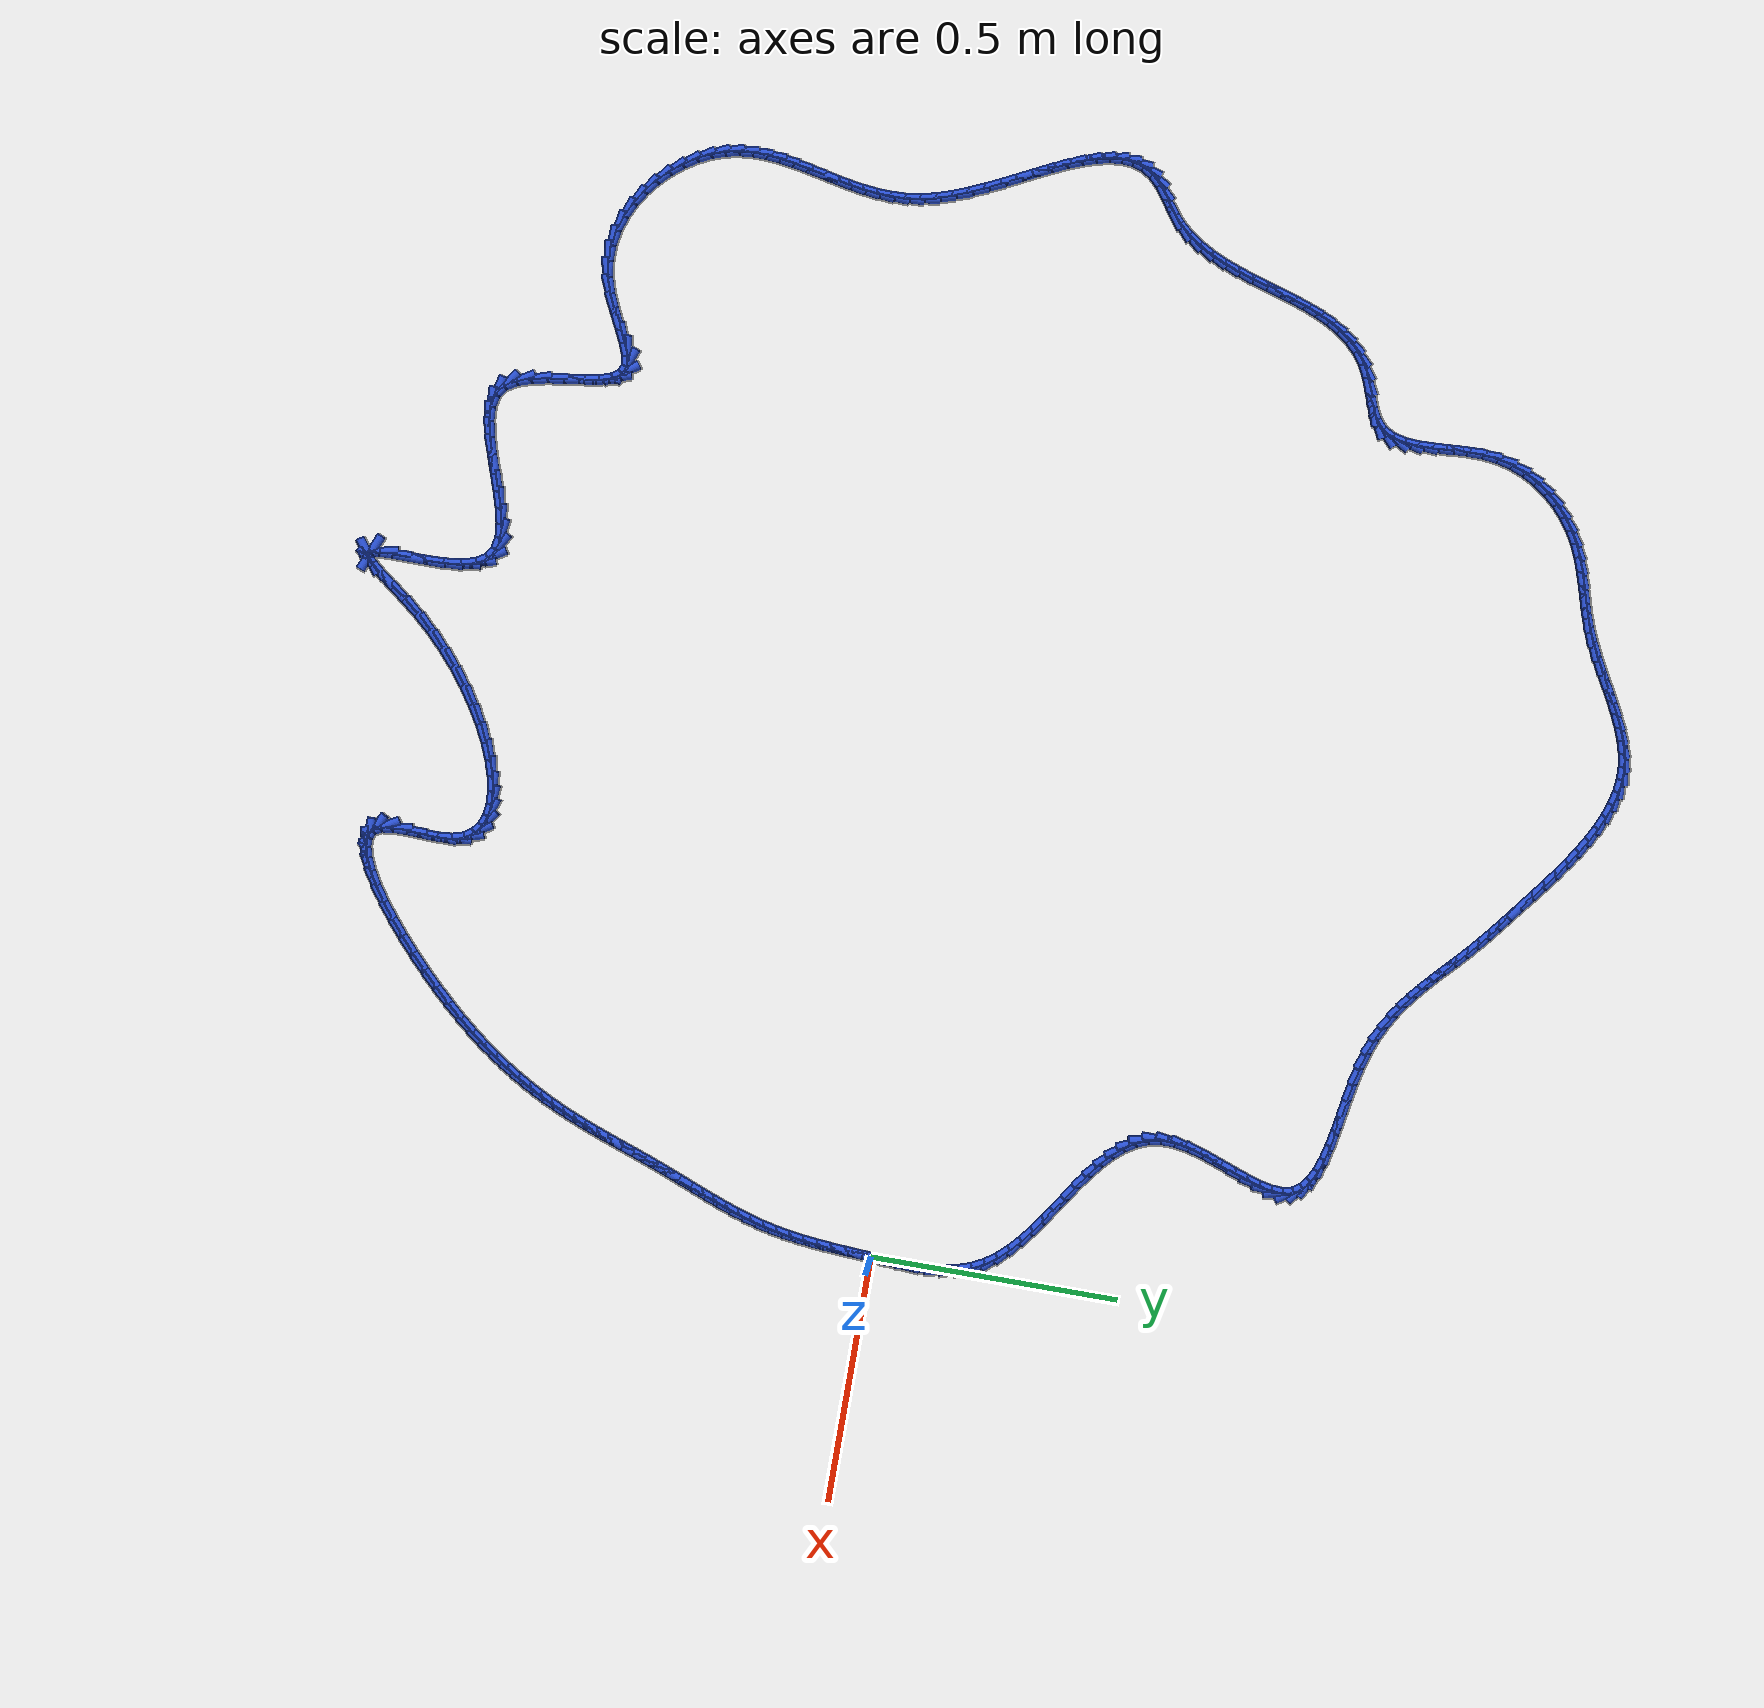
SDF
<sdf version="1.6">
 <world name="default">
  <light name="sun" type="directional">
   <pose>0 0 10 0 -0 0</pose>
   <diffuse>0.8 0.8 0.8 1</diffuse>
   <specular>0.2 0.2 0.2 1</specular>
   <attenuation>
    <range>1000</range>
    <constant>0.9</constant>
    <linear>0.01</linear>
    <quadratic>0.001</quadratic>
   </attenuation>
   <direction>-0.5 0.1 -0.9</direction>
  </light>
  <model name="ground_plane">
   <static>1</static>
   <link name="link">
    <collision name="collision">
     <geometry><plane><normal>0 0 1</normal><size>100 100</size></plane></geometry>
     <surface><friction><ode><mu>100</mu><mu2>50</mu2></ode></friction></surface>
    </collision>
    <visual name="visual">
     <cast_shadows>0</cast_shadows>
     <geometry><plane><normal>0 0 1</normal><size>100 100</size></plane></geometry>
     <material>
      <script><uri>file://media/materials/scripts/gazebo.material</uri><name>Gazebo/WhiteGlow</name></script>
     </material>
    </visual>
   </link>
  </model>
  <gravity>0 0 -9.8</gravity>
  <magnetic_field>6e-06 2.3e-05 -4.2e-05</magnetic_field>
  <atmosphere type="adiabatic"/>
  <physics name="default_physics" default="0" type="ode">
   <max_step_size>0.001</max_step_size>
   <real_time_factor>1</real_time_factor>
   <real_time_update_rate>1000</real_time_update_rate>
  </physics>
  <scene><ambient>0.4 0.4 0.4 1</ambient><background>0.7 0.7 0.7 1</background><shadows>1</shadows></scene>
  <spherical_coordinates>
   <surface_model>EARTH_WGS84</surface_model>
   <latitude_deg>0</latitude_deg>
   <longitude_deg>0</longitude_deg>
   <elevation>0</elevation>
   <heading_deg>0</heading_deg>
  </spherical_coordinates>
  <model name="line">
   <link name="link_0">
    <pose>3.903127820947816e-18 1.3877787807814457e-17 0.01 0 1.57 1.5122501408188502</pose>
    <collision name="collision">
     <geometry><cylinder><radius>0.01</radius><length>0.08</length></cylinder></geometry>
    </collision>
    <visual name="visual">
     <material>
      <script><name>Gazebo/Blue</name><uri>file://media/materials/scripts/gazebo.material</uri></script>
     </material>
     <geometry><cylinder><radius>0.01</radius><length>0.08</length></cylinder></geometry>
    </visual>
   </link>
   <link name="link_1">
    <pose>0.0017442463922473731 0.029758608789196915 0.01 0 1.57 1.5258216991188778</pose>
    <collision name="collision">
     <geometry><cylinder><radius>0.01</radius><length>0.08</length></cylinder></geometry>
    </collision>
    <visual name="visual">
     <material>
      <script><name>Gazebo/Blue</name><uri>file://media/materials/scripts/gazebo.material</uri></script>
     </material>
     <geometry><cylinder><radius>0.01</radius><length>0.08</length></cylinder></geometry>
    </visual>
   </link>
   <link name="link_2">
    <pose>0.0030905800420535897 0.05967382646153182 0.01 0 1.57 1.556951481879732</pose>
    <collision name="collision">
     <geometry><cylinder><radius>0.01</radius><length>0.08</length></cylinder></geometry>
    </collision>
    <visual name="visual">
     <material>
      <script><name>Gazebo/Blue</name><uri>file://media/materials/scripts/gazebo.material</uri></script>
     </material>
     <geometry><cylinder><radius>0.01</radius><length>0.08</length></cylinder></geometry>
    </visual>
   </link>
   <link name="link_3">
    <pose>0.003502925631898839 0.08945525384030607 0.01 0 1.57 -1.5347827048240574</pose>
    <collision name="collision">
     <geometry><cylinder><radius>0.01</radius><length>0.08</length></cylinder></geometry>
    </collision>
    <visual name="visual">
     <material>
      <script><name>Gazebo/Blue</name><uri>file://media/materials/scripts/gazebo.material</uri></script>
     </material>
     <geometry><cylinder><radius>0.01</radius><length>0.08</length></cylinder></geometry>
    </visual>
   </link>
   <link name="link_4">
    <pose>0.0024452078442633073 0.1188124917488211 0.01 0 1.57 -1.4642331994224542</pose>
    <collision name="collision">
     <geometry><cylinder><radius>0.01</radius><length>0.08</length></cylinder></geometry>
    </collision>
    <visual name="visual">
     <material>
      <script><name>Gazebo/Blue</name><uri>file://media/materials/scripts/gazebo.material</uri></script>
     </material>
     <geometry><cylinder><radius>0.01</radius><length>0.08</length></cylinder></geometry>
    </visual>
   </link>
   <link name="link_5">
    <pose>-0.0006186486383728089 0.14745514101037832 0.01 0 1.57 -1.3706698530665402</pose>
    <collision name="collision">
     <geometry><cylinder><radius>0.01</radius><length>0.08</length></cylinder></geometry>
    </collision>
    <visual name="visual">
     <material>
      <script><name>Gazebo/Blue</name><uri>file://media/materials/scripts/gazebo.material</uri></script>
     </material>
     <geometry><cylinder><radius>0.01</radius><length>0.08</length></cylinder></geometry>
    </visual>
   </link>
   <link name="link_6">
    <pose>-0.006224719133529337 0.17509280244827907 0.01 0 1.57 -1.2523428880414997</pose>
    <collision name="collision">
     <geometry><cylinder><radius>0.01</radius><length>0.08</length></cylinder></geometry>
    </collision>
    <visual name="visual">
     <material>
      <script><name>Gazebo/Blue</name><uri>file://media/materials/scripts/gazebo.material</uri></script>
     </material>
     <geometry><cylinder><radius>0.01</radius><length>0.08</length></cylinder></geometry>
    </visual>
   </link>
   <link name="link_7">
    <pose>-0.014909078958726068 0.20143507688582474 0.01 0 1.57 -1.109749597400508</pose>
    <collision name="collision">
     <geometry><cylinder><radius>0.01</radius><length>0.08</length></cylinder></geometry>
    </collision>
    <visual name="visual">
     <material>
      <script><name>Gazebo/Blue</name><uri>file://media/materials/scripts/gazebo.material</uri></script>
     </material>
     <geometry><cylinder><radius>0.01</radius><length>0.08</length></cylinder></geometry>
    </visual>
   </link>
   <link name="link_8">
    <pose>-0.027207105350043455 0.22619189472226361 0.01 0 1.57 -0.9590329431514204</pose>
    <collision name="collision">
     <geometry><cylinder><radius>0.01</radius><length>0.08</length></cylinder></geometry>
    </collision>
    <visual name="visual">
     <material>
      <script><name>Gazebo/Blue</name><uri>file://media/materials/scripts/gazebo.material</uri></script>
     </material>
     <geometry><cylinder><radius>0.01</radius><length>0.08</length></cylinder></geometry>
    </visual>
   </link>
   <link name="link_9">
    <pose>-0.043357625138385945 0.24921319277308443 0.01 0 1.57 -0.834334397316058</pose>
    <collision name="collision">
     <geometry><cylinder><radius>0.01</radius><length>0.08</length></cylinder></geometry>
    </collision>
    <visual name="visual">
     <material>
      <script><name>Gazebo/Blue</name><uri>file://media/materials/scripts/gazebo.material</uri></script>
     </material>
     <geometry><cylinder><radius>0.01</radius><length>0.08</length></cylinder></geometry>
    </visual>
   </link>
   <link name="link_10">
    <pose>-0.06284337221791567 0.27070587200074914 0.01 0 1.57 -0.7392663352473778</pose>
    <collision name="collision">
     <geometry><cylinder><radius>0.01</radius><length>0.08</length></cylinder></geometry>
    </collision>
    <visual name="visual">
     <material>
      <script><name>Gazebo/Blue</name><uri>file://media/materials/scripts/gazebo.material</uri></script>
     </material>
     <geometry><cylinder><radius>0.01</radius><length>0.08</length></cylinder></geometry>
    </visual>
   </link>
   <link name="link_11">
    <pose>-0.0850283293911544 0.2909328977482601 0.01 0 1.57 -0.6703454896885207</pose>
    <collision name="collision">
     <geometry><cylinder><radius>0.01</radius><length>0.08</length></cylinder></geometry>
    </collision>
    <visual name="visual">
     <material>
      <script><name>Gazebo/Blue</name><uri>file://media/materials/scripts/gazebo.material</uri></script>
     </material>
     <geometry><cylinder><radius>0.01</radius><length>0.08</length></cylinder></geometry>
    </visual>
   </link>
   <link name="link_12">
    <pose>-0.10927647946062406 0.31015723535861955 0.01 0 1.57 -0.6239815044802735</pose>
    <collision name="collision">
     <geometry><cylinder><radius>0.01</radius><length>0.08</length></cylinder></geometry>
    </collision>
    <visual name="visual">
     <material>
      <script><name>Gazebo/Blue</name><uri>file://media/materials/scripts/gazebo.material</uri></script>
     </material>
     <geometry><cylinder><radius>0.01</radius><length>0.08</length></cylinder></geometry>
    </visual>
   </link>
   <link name="link_13">
    <pose>-0.13495180522884656 0.3286418501748298 0.01 0 1.57 -0.5974517177394485</pose>
    <collision name="collision">
     <geometry><cylinder><radius>0.01</radius><length>0.08</length></cylinder></geometry>
    </collision>
    <visual name="visual">
     <material>
      <script><name>Gazebo/Blue</name><uri>file://media/materials/scripts/gazebo.material</uri></script>
     </material>
     <geometry><cylinder><radius>0.01</radius><length>0.08</length></cylinder></geometry>
    </visual>
   </link>
   <link name="link_14">
    <pose>-0.16141828949834358 0.34664970753989316 0.01 0 1.57 -0.5892060763753333</pose>
    <collision name="collision">
     <geometry><cylinder><radius>0.01</radius><length>0.08</length></cylinder></geometry>
    </collision>
    <visual name="visual">
     <material>
      <script><name>Gazebo/Blue</name><uri>file://media/materials/scripts/gazebo.material</uri></script>
     </material>
     <geometry><cylinder><radius>0.01</radius><length>0.08</length></cylinder></geometry>
    </visual>
   </link>
   <link name="link_15">
    <pose>-0.18803991507163711 0.36444377279681206 0.01 0 1.57 -0.5989409986802355</pose>
    <collision name="collision">
     <geometry><cylinder><radius>0.01</radius><length>0.08</length></cylinder></geometry>
    </collision>
    <visual name="visual">
     <material>
      <script><name>Gazebo/Blue</name><uri>file://media/materials/scripts/gazebo.material</uri></script>
     </material>
     <geometry><cylinder><radius>0.01</radius><length>0.08</length></cylinder></geometry>
    </visual>
   </link>
   <link name="link_16">
    <pose>-0.21418066475124908 0.3822870112885886 0.01 0 1.57 -0.6276507489593236</pose>
    <collision name="collision">
     <geometry><cylinder><radius>0.01</radius><length>0.08</length></cylinder></geometry>
    </collision>
    <visual name="visual">
     <material>
      <script><name>Gazebo/Blue</name><uri>file://media/materials/scripts/gazebo.material</uri></script>
     </material>
     <geometry><cylinder><radius>0.01</radius><length>0.08</length></cylinder></geometry>
    </visual>
   </link>
   <link name="link_17">
    <pose>-0.23920452133970124 0.4004423883582253 0.01 0 1.57 -0.6777136943184412</pose>
    <collision name="collision">
     <geometry><cylinder><radius>0.01</radius><length>0.08</length></cylinder></geometry>
    </collision>
    <visual name="visual">
     <material>
      <script><name>Gazebo/Blue</name><uri>file://media/materials/scripts/gazebo.material</uri></script>
     </material>
     <geometry><cylinder><radius>0.01</radius><length>0.08</length></cylinder></geometry>
    </visual>
   </link>
   <link name="link_18">
    <pose>-0.26247546763951546 0.41917286934872444 0.01 0 1.57 -0.7529386144405495</pose>
    <collision name="collision">
     <geometry><cylinder><radius>0.01</radius><length>0.08</length></cylinder></geometry>
    </collision>
    <visual name="visual">
     <material>
      <script><name>Gazebo/Blue</name><uri>file://media/materials/scripts/gazebo.material</uri></script>
     </material>
     <geometry><cylinder><radius>0.01</radius><length>0.08</length></cylinder></geometry>
    </visual>
   </link>
   <link name="link_19">
    <pose>-0.2833574864532136 0.4387414196030882 0.01 0 1.57 -0.858270572618717</pose>
    <collision name="collision">
     <geometry><cylinder><radius>0.01</radius><length>0.08</length></cylinder></geometry>
    </collision>
    <visual name="visual">
     <material>
      <script><name>Gazebo/Blue</name><uri>file://media/materials/scripts/gazebo.material</uri></script>
     </material>
     <geometry><cylinder><radius>0.01</radius><length>0.08</length></cylinder></geometry>
    </visual>
   </link>
   <link name="link_20">
    <pose>-0.30121456058331764 0.45941100446431904 0.01 0 1.57 -0.998442633605758</pose>
    <collision name="collision">
     <geometry><cylinder><radius>0.01</radius><length>0.08</length></cylinder></geometry>
    </collision>
    <visual name="visual">
     <material>
      <script><name>Gazebo/Blue</name><uri>file://media/materials/scripts/gazebo.material</uri></script>
     </material>
     <geometry><cylinder><radius>0.01</radius><length>0.08</length></cylinder></geometry>
    </visual>
   </link>
   <link name="link_21">
    <pose>-0.31541067283234936 0.4814445892754193 0.01 0 1.57 -1.1745450551258132</pose>
    <collision name="collision">
     <geometry><cylinder><radius>0.01</radius><length>0.08</length></cylinder></geometry>
    </collision>
    <visual name="visual">
     <material>
      <script><name>Gazebo/Blue</name><uri>file://media/materials/scripts/gazebo.material</uri></script>
     </material>
     <geometry><cylinder><radius>0.01</radius><length>0.08</length></cylinder></geometry>
    </visual>
   </link>
   <link name="link_22">
    <pose>-0.32530980600283055 0.505105139379391 0.01 0 1.57 -1.3788241931452603</pose>
    <collision name="collision">
     <geometry><cylinder><radius>0.01</radius><length>0.08</length></cylinder></geometry>
    </collision>
    <visual name="visual">
     <material>
      <script><name>Gazebo/Blue</name><uri>file://media/materials/scripts/gazebo.material</uri></script>
     </material>
     <geometry><cylinder><radius>0.01</radius><length>0.08</length></cylinder></geometry>
    </visual>
   </link>
   <link name="link_23">
    <pose>-0.3302759428972832 0.530655620119237 0.01 0 1.57 1.5558913883083831</pose>
    <collision name="collision">
     <geometry><cylinder><radius>0.01</radius><length>0.08</length></cylinder></geometry>
    </collision>
    <visual name="visual">
     <material>
      <script><name>Gazebo/Blue</name><uri>file://media/materials/scripts/gazebo.material</uri></script>
     </material>
     <geometry><cylinder><radius>0.01</radius><length>0.08</length></cylinder></geometry>
    </visual>
   </link>
   <link name="link_24">
    <pose>-0.3298643063111231 0.5582710378819528 0.01 0 1.57 1.4017919769859504</pose>
    <collision name="collision">
     <geometry><cylinder><radius>0.01</radius><length>0.08</length></cylinder></geometry>
    </collision>
    <visual name="visual">
     <material>
      <script><name>Gazebo/Blue</name><uri>file://media/materials/scripts/gazebo.material</uri></script>
     </material>
     <geometry><cylinder><radius>0.01</radius><length>0.08</length></cylinder></geometry>
    </visual>
   </link>
   <link name="link_25">
    <pose>-0.32486710538476343 0.5875574593372003 0.01 0 1.57 1.3037899901988474</pose>
    <collision name="collision">
     <geometry><cylinder><radius>0.01</radius><length>0.08</length></cylinder></geometry>
    </collision>
    <visual name="visual">
     <material>
      <script><name>Gazebo/Blue</name><uri>file://media/materials/scripts/gazebo.material</uri></script>
     </material>
     <geometry><cylinder><radius>0.01</radius><length>0.08</length></cylinder></geometry>
    </visual>
   </link>
   <link name="link_26">
    <pose>-0.31656875961875974 0.6178945638349262 0.01 0 1.57 1.2473448263265035</pose>
    <collision name="collision">
     <geometry><cylinder><radius>0.01</radius><length>0.08</length></cylinder></geometry>
    </collision>
    <visual name="visual">
     <material>
      <script><name>Gazebo/Blue</name><uri>file://media/materials/scripts/gazebo.material</uri></script>
     </material>
     <geometry><cylinder><radius>0.01</radius><length>0.08</length></cylinder></geometry>
    </visual>
   </link>
   <link name="link_27">
    <pose>-0.30625495012892845 0.6486614504575322 0.01 0 1.57 1.2241896860069106</pose>
    <collision name="collision">
     <geometry><cylinder><radius>0.01</radius><length>0.08</length></cylinder></geometry>
    </collision>
    <visual name="visual">
     <material>
      <script><name>Gazebo/Blue</name><uri>file://media/materials/scripts/gazebo.material</uri></script>
     </material>
     <geometry><cylinder><radius>0.01</radius><length>0.08</length></cylinder></geometry>
    </visual>
   </link>
   <link name="link_28">
    <pose>-0.29521135803108595 0.6792372182874196 0.01 0 1.57 1.2320164432173886</pose>
    <collision name="collision">
     <geometry><cylinder><radius>0.01</radius><length>0.08</length></cylinder></geometry>
    </collision>
    <visual name="visual">
     <material>
      <script><name>Gazebo/Blue</name><uri>file://media/materials/scripts/gazebo.material</uri></script>
     </material>
     <geometry><cylinder><radius>0.01</radius><length>0.08</length></cylinder></geometry>
    </visual>
   </link>
   <link name="link_29">
    <pose>-0.2847236644410487 0.7090009664069894 0.01 0 1.57 1.2745904224871125</pose>
    <collision name="collision">
     <geometry><cylinder><radius>0.01</radius><length>0.08</length></cylinder></geometry>
    </collision>
    <visual name="visual">
     <material>
      <script><name>Gazebo/Blue</name><uri>file://media/materials/scripts/gazebo.material</uri></script>
     </material>
     <geometry><cylinder><radius>0.01</radius><length>0.08</length></cylinder></geometry>
    </visual>
   </link>
   <link name="link_30">
    <pose>-0.2760775504746334 0.7373317938986432 0.01 0 1.57 1.3637792754838602</pose>
    <collision name="collision">
     <geometry><cylinder><radius>0.01</radius><length>0.08</length></cylinder></geometry>
    </collision>
    <visual name="visual">
     <material>
      <script><name>Gazebo/Blue</name><uri>file://media/materials/scripts/gazebo.material</uri></script>
     </material>
     <geometry><cylinder><radius>0.01</radius><length>0.08</length></cylinder></geometry>
    </visual>
   </link>
   <link name="link_31">
    <pose>-0.2705586972476563 0.7636087998447827 0.01 0 1.57 1.5239744548455967</pose>
    <collision name="collision">
     <geometry><cylinder><radius>0.01</radius><length>0.08</length></cylinder></geometry>
    </collision>
    <visual name="visual">
     <material>
      <script><name>Gazebo/Blue</name><uri>file://media/materials/scripts/gazebo.material</uri></script>
     </material>
     <geometry><cylinder><radius>0.01</radius><length>0.08</length></cylinder></geometry>
    </visual>
   </link>
   <link name="link_32">
    <pose>-0.269452785875934 0.787211083327809 0.01 0 1.57 -1.3485402495209033</pose>
    <collision name="collision">
     <geometry><cylinder><radius>0.01</radius><length>0.08</length></cylinder></geometry>
    </collision>
    <visual name="visual">
     <material>
      <script><name>Gazebo/Blue</name><uri>file://media/materials/scripts/gazebo.material</uri></script>
     </material>
     <geometry><cylinder><radius>0.01</radius><length>0.08</length></cylinder></geometry>
    </visual>
   </link>
   <link name="link_33">
    <pose>-0.2740422774299361 0.8075195102532613 0.01 0 1.57 -0.9907491317451966</pose>
    <collision name="collision">
     <geometry><cylinder><radius>0.01</radius><length>0.08</length></cylinder></geometry>
    </collision>
    <visual name="visual">
     <material>
      <script><name>Gazebo/Blue</name><uri>file://media/materials/scripts/gazebo.material</uri></script>
     </material>
     <geometry><cylinder><radius>0.01</radius><length>0.08</length></cylinder></geometry>
    </visual>
   </link>
   <link name="link_34">
    <pose>-0.28500318793580537 0.8242476999573504 0.01 0 1.57 -0.6831482211758472</pose>
    <collision name="collision">
     <geometry><cylinder><radius>0.01</radius><length>0.08</length></cylinder></geometry>
    </collision>
    <visual name="visual">
     <material>
      <script><name>Gazebo/Blue</name><uri>file://media/materials/scripts/gazebo.material</uri></script>
     </material>
     <geometry><cylinder><radius>0.01</radius><length>0.08</length></cylinder></geometry>
    </visual>
   </link>
   <link name="link_35">
    <pose>-0.3016941105527869 0.8378321352619525 0.01 0 1.57 -0.46987348821937597</pose>
    <collision name="collision">
     <geometry><cylinder><radius>0.01</radius><length>0.08</length></cylinder></geometry>
    </collision>
    <visual name="visual">
     <material>
      <script><name>Gazebo/Blue</name><uri>file://media/materials/scripts/gazebo.material</uri></script>
     </material>
     <geometry><cylinder><radius>0.01</radius><length>0.08</length></cylinder></geometry>
    </visual>
   </link>
   <link name="link_36">
    <pose>-0.3233007778020779 0.8488041467758555 0.01 0 1.57 -0.3329644847193989</pose>
    <collision name="collision">
     <geometry><cylinder><radius>0.01</radius><length>0.08</length></cylinder></geometry>
    </collision>
    <visual name="visual">
     <material>
      <script><name>Gazebo/Blue</name><uri>file://media/materials/scripts/gazebo.material</uri></script>
     </material>
     <geometry><cylinder><radius>0.01</radius><length>0.08</length></cylinder></geometry>
    </visual>
   </link>
   <link name="link_37">
    <pose>-0.34900892220487634 0.857695065107848 0.01 0 1.57 -0.24797298807616366</pose>
    <collision name="collision">
     <geometry><cylinder><radius>0.01</radius><length>0.08</length></cylinder></geometry>
    </collision>
    <visual name="visual">
     <material>
      <script><name>Gazebo/Blue</name><uri>file://media/materials/scripts/gazebo.material</uri></script>
     </material>
     <geometry><cylinder><radius>0.01</radius><length>0.08</length></cylinder></geometry>
    </visual>
   </link>
   <link name="link_38">
    <pose>-0.37800427628237915 0.8650362208667182 0.01 0 1.57 -0.1982834917036327</pose>
    <collision name="collision">
     <geometry><cylinder><radius>0.01</radius><length>0.08</length></cylinder></geometry>
    </collision>
    <visual name="visual">
     <material>
      <script><name>Gazebo/Blue</name><uri>file://media/materials/scripts/gazebo.material</uri></script>
     </material>
     <geometry><cylinder><radius>0.01</radius><length>0.08</length></cylinder></geometry>
    </visual>
   </link>
   <link name="link_39">
    <pose>-0.4094725725557843 0.871358944661254 0.01 0 1.57 -0.1743702497080753</pose>
    <collision name="collision">
     <geometry><cylinder><radius>0.01</radius><length>0.08</length></cylinder></geometry>
    </collision>
    <visual name="visual">
     <material>
      <script><name>Gazebo/Blue</name><uri>file://media/materials/scripts/gazebo.material</uri></script>
     </material>
     <geometry><cylinder><radius>0.01</radius><length>0.08</length></cylinder></geometry>
    </visual>
   </link>
   <link name="link_40">
    <pose>-0.4425995435462888 0.8771945671002439 0.01 0 1.57 -0.1713845588244232</pose>
    <collision name="collision">
     <geometry><cylinder><radius>0.01</radius><length>0.08</length></cylinder></geometry>
    </collision>
    <visual name="visual">
     <material>
      <script><name>Gazebo/Blue</name><uri>file://media/materials/scripts/gazebo.material</uri></script>
     </material>
     <geometry><cylinder><radius>0.01</radius><length>0.08</length></cylinder></geometry>
    </visual>
   </link>
   <link name="link_41">
    <pose>-0.4765709217750905 0.8830744187924763 0.01 0 1.57 -0.1876235095575148</pose>
    <collision name="collision">
     <geometry><cylinder><radius>0.01</radius><length>0.08</length></cylinder></geometry>
    </collision>
    <visual name="visual">
     <material>
      <script><name>Gazebo/Blue</name><uri>file://media/materials/scripts/gazebo.material</uri></script>
     </material>
     <geometry><cylinder><radius>0.01</radius><length>0.08</length></cylinder></geometry>
    </visual>
   </link>
   <link name="link_42">
    <pose>-0.5105724397633867 0.8895298303467392 0.01 0 1.57 -0.22384570779319432</pose>
    <collision name="collision">
     <geometry><cylinder><radius>0.01</radius><length>0.08</length></cylinder></geometry>
    </collision>
    <visual name="visual">
     <material>
      <script><name>Gazebo/Blue</name><uri>file://media/materials/scripts/gazebo.material</uri></script>
     </material>
     <geometry><cylinder><radius>0.01</radius><length>0.08</length></cylinder></geometry>
    </visual>
   </link>
   <link name="link_43">
    <pose>-0.5437898300323747 0.8970921323718206 0.01 0 1.57 -0.2831619745207348</pose>
    <collision name="collision">
     <geometry><cylinder><radius>0.01</radius><length>0.08</length></cylinder></geometry>
    </collision>
    <visual name="visual">
     <material>
      <script><name>Gazebo/Blue</name><uri>file://media/materials/scripts/gazebo.material</uri></script>
     </material>
     <geometry><cylinder><radius>0.01</radius><length>0.08</length></cylinder></geometry>
    </visual>
   </link>
   <link name="link_44">
    <pose>-0.5754088251032525 0.9062926554765094 0.01 0 1.57 -0.36552655215878593</pose>
    <collision name="collision">
     <geometry><cylinder><radius>0.01</radius><length>0.08</length></cylinder></geometry>
    </collision>
    <visual name="visual">
     <material>
      <script><name>Gazebo/Blue</name><uri>file://media/materials/scripts/gazebo.material</uri></script>
     </material>
     <geometry><cylinder><radius>0.01</radius><length>0.08</length></cylinder></geometry>
    </visual>
   </link>
   <link name="link_45">
    <pose>-0.6047886409805884 0.9175370636598086 0.01 0 1.57 -0.4501227859402464</pose>
    <collision name="collision">
     <geometry><cylinder><radius>0.01</radius><length>0.08</length></cylinder></geometry>
    </collision>
    <visual name="visual">
     <material>
      <script><name>Gazebo/Blue</name><uri>file://media/materials/scripts/gazebo.material</uri></script>
     </material>
     <geometry><cylinder><radius>0.01</radius><length>0.08</length></cylinder></geometry>
    </visual>
   </link>
   <link name="link_46">
    <pose>-0.6320247238511203 0.9306977162555383 0.01 0 1.57 -0.528104487492749</pose>
    <collision name="collision">
     <geometry><cylinder><radius>0.01</radius><length>0.08</length></cylinder></geometry>
    </collision>
    <visual name="visual">
     <material>
      <script><name>Gazebo/Blue</name><uri>file://media/materials/scripts/gazebo.material</uri></script>
     </material>
     <geometry><cylinder><radius>0.01</radius><length>0.08</length></cylinder></geometry>
    </visual>
   </link>
   <link name="link_47">
    <pose>-0.6574077881415934 0.9455055257159847 0.01 0 1.57 -0.5968252054183288</pose>
    <collision name="collision">
     <geometry><cylinder><radius>0.01</radius><length>0.08</length></cylinder></geometry>
    </collision>
    <visual name="visual">
     <material>
      <script><name>Gazebo/Blue</name><uri>file://media/materials/scripts/gazebo.material</uri></script>
     </material>
     <geometry><cylinder><radius>0.01</radius><length>0.08</length></cylinder></geometry>
    </visual>
   </link>
   <link name="link_48">
    <pose>-0.6812285496905248 0.9616914034707866 0.01 0 1.57 -0.6542825904733287</pose>
    <collision name="collision">
     <geometry><cylinder><radius>0.01</radius><length>0.08</length></cylinder></geometry>
    </collision>
    <visual name="visual">
     <material>
      <script><name>Gazebo/Blue</name><uri>file://media/materials/scripts/gazebo.material</uri></script>
     </material>
     <geometry><cylinder><radius>0.01</radius><length>0.08</length></cylinder></geometry>
    </visual>
   </link>
   <link name="link_49">
    <pose>-0.7037777243364307 0.9789862609495829 0.01 0 1.57 -0.69913191488999</pose>
    <collision name="collision">
     <geometry><cylinder><radius>0.01</radius><length>0.08</length></cylinder></geometry>
    </collision>
    <visual name="visual">
     <material>
      <script><name>Gazebo/Blue</name><uri>file://media/materials/scripts/gazebo.material</uri></script>
     </material>
     <geometry><cylinder><radius>0.01</radius><length>0.08</length></cylinder></geometry>
    </visual>
   </link>
   <link name="link_50">
    <pose>-0.7253460279178282 0.997121009582012 0.01 0 1.57 -0.7305670219041283</pose>
    <collision name="collision">
     <geometry><cylinder><radius>0.01</radius><length>0.08</length></cylinder></geometry>
    </collision>
    <visual name="visual">
     <material>
      <script><name>Gazebo/Blue</name><uri>file://media/materials/scripts/gazebo.material</uri></script>
     </material>
     <geometry><cylinder><radius>0.01</radius><length>0.08</length></cylinder></geometry>
    </visual>
   </link>
   <link name="link_51">
    <pose>-0.7462241762732335 1.0158265607977124 0.01 0 1.57 -0.7481504263059927</pose>
    <collision name="collision">
     <geometry><cylinder><radius>0.01</radius><length>0.08</length></cylinder></geometry>
    </collision>
    <visual name="visual">
     <material>
      <script><name>Gazebo/Blue</name><uri>file://media/materials/scripts/gazebo.material</uri></script>
     </material>
     <geometry><cylinder><radius>0.01</radius><length>0.08</length></cylinder></geometry>
    </visual>
   </link>
   <link name="link_52">
    <pose>-0.7667028852411639 1.0348338260263228 0.01 0 1.57 -0.7516606794067981</pose>
    <collision name="collision">
     <geometry><cylinder><radius>0.01</radius><length>0.08</length></cylinder></geometry>
    </collision>
    <visual name="visual">
     <material>
      <script><name>Gazebo/Blue</name><uri>file://media/materials/scripts/gazebo.material</uri></script>
     </material>
     <geometry><cylinder><radius>0.01</radius><length>0.08</length></cylinder></geometry>
    </visual>
   </link>
   <link name="link_53">
    <pose>-0.7870728706601353 1.0538737166974819 0.01 0 1.57 -0.7409976301524455</pose>
    <collision name="collision">
     <geometry><cylinder><radius>0.01</radius><length>0.08</length></cylinder></geometry>
    </collision>
    <visual name="visual">
     <material>
      <script><name>Gazebo/Blue</name><uri>file://media/materials/scripts/gazebo.material</uri></script>
     </material>
     <geometry><cylinder><radius>0.01</radius><length>0.08</length></cylinder></geometry>
    </visual>
   </link>
   <link name="link_54">
    <pose>-0.8076248483686651 1.0726771442408285 0.01 0 1.57 -0.7172671707336774</pose>
    <collision name="collision">
     <geometry><cylinder><radius>0.01</radius><length>0.08</length></cylinder></geometry>
    </collision>
    <visual name="visual">
     <material>
      <script><name>Gazebo/Blue</name><uri>file://media/materials/scripts/gazebo.material</uri></script>
     </material>
     <geometry><cylinder><radius>0.01</radius><length>0.08</length></cylinder></geometry>
    </visual>
   </link>
   <link name="link_55">
    <pose>-0.8286344472180314 1.0910026491040457 0.01 0 1.57 -0.6928272018302386</pose>
    <collision name="collision">
     <geometry><cylinder><radius>0.01</radius><length>0.08</length></cylinder></geometry>
    </collision>
    <visual name="visual">
     <material>
      <script><name>Gazebo/Blue</name><uri>file://media/materials/scripts/gazebo.material</uri></script>
     </material>
     <geometry><cylinder><radius>0.01</radius><length>0.08</length></cylinder></geometry>
    </visual>
   </link>
   <link name="link_56">
    <pose>-0.8502109852501272 1.1089133391266282 0.01 0 1.57 -0.6755151028071706</pose>
    <collision name="collision">
     <geometry><cylinder><radius>0.01</radius><length>0.08</length></cylinder></geometry>
    </collision>
    <visual name="visual">
     <material>
      <script><name>Gazebo/Blue</name><uri>file://media/materials/scripts/gazebo.material</uri></script>
     </material>
     <geometry><cylinder><radius>0.01</radius><length>0.08</length></cylinder></geometry>
    </visual>
   </link>
   <link name="link_57">
    <pose>-0.8723606410530319 1.126661202922312 0.01 0 1.57 -0.6654956386654387</pose>
    <collision name="collision">
     <geometry><cylinder><radius>0.01</radius><length>0.08</length></cylinder></geometry>
    </collision>
    <visual name="visual">
     <material>
      <script><name>Gazebo/Blue</name><uri>file://media/materials/scripts/gazebo.material</uri></script>
     </material>
     <geometry><cylinder><radius>0.01</radius><length>0.08</length></cylinder></geometry>
    </visual>
   </link>
   <link name="link_58">
    <pose>-0.8950880517293283 1.1445010520495262 0.01 0 1.57 -0.662536947512708</pose>
    <collision name="collision">
     <geometry><cylinder><radius>0.01</radius><length>0.08</length></cylinder></geometry>
    </collision>
    <visual name="visual">
     <material>
      <script><name>Gazebo/Blue</name><uri>file://media/materials/scripts/gazebo.material</uri></script>
     </material>
     <geometry><cylinder><radius>0.01</radius><length>0.08</length></cylinder></geometry>
    </visual>
   </link>
   <link name="link_59">
    <pose>-0.9183977564601404 1.1626867706511839 0.01 0 1.57 -0.6619359870756996</pose>
    <collision name="collision">
     <geometry><cylinder><radius>0.01</radius><length>0.08</length></cylinder></geometry>
    </collision>
    <visual name="visual">
     <material>
      <script><name>Gazebo/Blue</name><uri>file://media/materials/scripts/gazebo.material</uri></script>
     </material>
     <geometry><cylinder><radius>0.01</radius><length>0.08</length></cylinder></geometry>
    </visual>
   </link>
   <link name="link_60">
    <pose>-0.9422753098212421 1.1812924394071784 0.01 0 1.57 -0.6542872192048848</pose>
    <collision name="collision">
     <geometry><cylinder><radius>0.01</radius><length>0.08</length></cylinder></geometry>
    </collision>
    <visual name="visual">
     <material>
      <script><name>Gazebo/Blue</name><uri>file://media/materials/scripts/gazebo.material</uri></script>
     </material>
     <geometry><cylinder><radius>0.01</radius><length>0.08</length></cylinder></geometry>
    </visual>
   </link>
   <link name="link_61">
    <pose>-0.9666647492893129 1.1999989299706912 0.01 0 1.57 -0.6384913722026878</pose>
    <collision name="collision">
     <geometry><cylinder><radius>0.01</radius><length>0.08</length></cylinder></geometry>
    </collision>
    <visual name="visual">
     <material>
      <script><name>Gazebo/Blue</name><uri>file://media/materials/scripts/gazebo.material</uri></script>
     </material>
     <geometry><cylinder><radius>0.01</radius><length>0.08</length></cylinder></geometry>
    </visual>
   </link>
   <link name="link_62">
    <pose>-0.9915046227353794 1.2184351218629248 0.01 0 1.57 -0.6142969545149345</pose>
    <collision name="collision">
     <geometry><cylinder><radius>0.01</radius><length>0.08</length></cylinder></geometry>
    </collision>
    <visual name="visual">
     <material>
      <script><name>Gazebo/Blue</name><uri>file://media/materials/scripts/gazebo.material</uri></script>
     </material>
     <geometry><cylinder><radius>0.01</radius><length>0.08</length></cylinder></geometry>
    </visual>
   </link>
   <link name="link_63">
    <pose>-1.016733478030469 1.2362298946050845 0.01 0 1.57 -0.5810531960142062</pose>
    <collision name="collision">
     <geometry><cylinder><radius>0.01</radius><length>0.08</length></cylinder></geometry>
    </collision>
    <visual name="visual">
     <material>
      <script><name>Gazebo/Blue</name><uri>file://media/materials/scripts/gazebo.material</uri></script>
     </material>
     <geometry><cylinder><radius>0.01</radius><length>0.08</length></cylinder></geometry>
    </visual>
   </link>
   <link name="link_64">
    <pose>-1.0422898630456086 1.253012127718374 0.01 0 1.57 -0.5377127125319096</pose>
    <collision name="collision">
     <geometry><cylinder><radius>0.01</radius><length>0.08</length></cylinder></geometry>
    </collision>
    <visual name="visual">
     <material>
      <script><name>Gazebo/Blue</name><uri>file://media/materials/scripts/gazebo.material</uri></script>
     </material>
     <geometry><cylinder><radius>0.01</radius><length>0.08</length></cylinder></geometry>
    </visual>
   </link>
   <link name="link_65">
    <pose>-1.068112325651825 1.2684107007239969 0.01 0 1.57 -0.48283149191226143</pose>
    <collision name="collision">
     <geometry><cylinder><radius>0.01</radius><length>0.08</length></cylinder></geometry>
    </collision>
    <visual name="visual">
     <material>
      <script><name>Gazebo/Blue</name><uri>file://media/materials/scripts/gazebo.material</uri></script>
     </material>
     <geometry><cylinder><radius>0.01</radius><length>0.08</length></cylinder></geometry>
    </visual>
   </link>
   <link name="link_66">
    <pose>-1.0941394137201457 1.2820544931431583 0.01 0 1.57 -0.4146021535567745</pose>
    <collision name="collision">
     <geometry><cylinder><radius>0.01</radius><length>0.08</length></cylinder></geometry>
    </collision>
    <visual name="visual">
     <material>
      <script><name>Gazebo/Blue</name><uri>file://media/materials/scripts/gazebo.material</uri></script>
     </material>
     <geometry><cylinder><radius>0.01</radius><length>0.08</length></cylinder></geometry>
    </visual>
   </link>
   <link name="link_67">
    <pose>-1.1203096751215975 1.2935723844970621 0.01 0 1.57 -0.330985382016928</pose>
    <collision name="collision">
     <geometry><cylinder><radius>0.01</radius><length>0.08</length></cylinder></geometry>
    </collision>
    <visual name="visual">
     <material>
      <script><name>Gazebo/Blue</name><uri>file://media/materials/scripts/gazebo.material</uri></script>
     </material>
     <geometry><cylinder><radius>0.01</radius><length>0.08</length></cylinder></geometry>
    </visual>
   </link>
   <link name="link_68">
    <pose>-1.1465616577272073 1.3025932543069123 0.01 0 1.57 -0.2300452656769726</pose>
    <collision name="collision">
     <geometry><cylinder><radius>0.01</radius><length>0.08</length></cylinder></geometry>
    </collision>
    <visual name="visual">
     <material>
      <script><name>Gazebo/Blue</name><uri>file://media/materials/scripts/gazebo.material</uri></script>
     </material>
     <geometry><cylinder><radius>0.01</radius><length>0.08</length></cylinder></geometry>
    </visual>
   </link>
   <link name="link_69">
    <pose>-1.172833909408002 1.3087459820939127 0.01 0 1.57 -0.11061587663504392</pose>
    <collision name="collision">
     <geometry><cylinder><radius>0.01</radius><length>0.08</length></cylinder></geometry>
    </collision>
    <visual name="visual">
     <material>
      <script><name>Gazebo/Blue</name><uri>file://media/materials/scripts/gazebo.material</uri></script>
     </material>
     <geometry><cylinder><radius>0.01</radius><length>0.08</length></cylinder></geometry>
    </visual>
   </link>
   <link name="link_70">
    <pose>-1.1990649780350098 1.3116594473792682 0.01 0 1.57 0.026565639706230975</pose>
    <collision name="collision">
     <geometry><cylinder><radius>0.01</radius><length>0.08</length></cylinder></geometry>
    </collision>
    <visual name="visual">
     <material>
      <script><name>Gazebo/Blue</name><uri>file://media/materials/scripts/gazebo.material</uri></script>
     </material>
     <geometry><cylinder><radius>0.01</radius><length>0.08</length></cylinder></geometry>
    </visual>
   </link>
   <link name="link_71">
    <pose>-1.2251937201918737 1.3109651572936094 0.01 0 1.57 0.16635604654185257</pose>
    <collision name="collision">
     <geometry><cylinder><radius>0.01</radius><length>0.08</length></cylinder></geometry>
    </collision>
    <visual name="visual">
     <material>
      <script><name>Gazebo/Blue</name><uri>file://media/materials/scripts/gazebo.material</uri></script>
     </material>
     <geometry><cylinder><radius>0.01</radius><length>0.08</length></cylinder></geometry>
    </visual>
   </link>
   <link name="link_72">
    <pose>-1.2511947974078241 1.3065993729918344 0.01 0 1.57 0.2822656990205532</pose>
    <collision name="collision">
     <geometry><cylinder><radius>0.01</radius><length>0.08</length></cylinder></geometry>
    </collision>
    <visual name="visual">
     <material>
      <script><name>Gazebo/Blue</name><uri>file://media/materials/scripts/gazebo.material</uri></script>
     </material>
     <geometry><cylinder><radius>0.01</radius><length>0.08</length></cylinder></geometry>
    </visual>
   </link>
   <link name="link_73">
    <pose>-1.2771115916532596 1.2990832701051274 0.01 0 1.57 0.37133186722553246</pose>
    <collision name="collision">
     <geometry><cylinder><radius>0.01</radius><length>0.08</length></cylinder></geometry>
    </collision>
    <visual name="visual">
     <material>
      <script><name>Gazebo/Blue</name><uri>file://media/materials/scripts/gazebo.material</uri></script>
     </material>
     <geometry><cylinder><radius>0.01</radius><length>0.08</length></cylinder></geometry>
    </visual>
   </link>
   <link name="link_74">
    <pose>-1.3029952674496195 1.2890042654978378 0.01 0 1.57 0.43558105416963316</pose>
    <collision name="collision">
     <geometry><cylinder><radius>0.01</radius><length>0.08</length></cylinder></geometry>
    </collision>
    <visual name="visual">
     <material>
      <script><name>Gazebo/Blue</name><uri>file://media/materials/scripts/gazebo.material</uri></script>
     </material>
     <geometry><cylinder><radius>0.01</radius><length>0.08</length></cylinder></geometry>
    </visual>
   </link>
   <link name="link_75">
    <pose>-1.328896989318343 1.2769497760343136 0.01 0 1.57 0.4776283532183465</pose>
    <collision name="collision">
     <geometry><cylinder><radius>0.01</radius><length>0.08</length></cylinder></geometry>
    </collision>
    <visual name="visual">
     <material>
      <script><name>Gazebo/Blue</name><uri>file://media/materials/scripts/gazebo.material</uri></script>
     </material>
     <geometry><cylinder><radius>0.01</radius><length>0.08</length></cylinder></geometry>
    </visual>
   </link>
   <link name="link_76">
    <pose>-1.354867921780871 1.263507218578904 0.01 0 1.57 0.4996888998927141</pose>
    <collision name="collision">
     <geometry><cylinder><radius>0.01</radius><length>0.08</length></cylinder></geometry>
    </collision>
    <visual name="visual">
     <material>
      <script><name>Gazebo/Blue</name><uri>file://media/materials/scripts/gazebo.material</uri></script>
     </material>
     <geometry><cylinder><radius>0.01</radius><length>0.08</length></cylinder></geometry>
    </visual>
   </link>
   <link name="link_77">
    <pose>-1.3809592293586415 1.2492640099959564 0.01 0 1.57 0.5031903470599809</pose>
    <collision name="collision">
     <geometry><cylinder><radius>0.01</radius><length>0.08</length></cylinder></geometry>
    </collision>
    <visual name="visual">
     <material>
      <script><name>Gazebo/Blue</name><uri>file://media/materials/scripts/gazebo.material</uri></script>
     </material>
     <geometry><cylinder><radius>0.01</radius><length>0.08</length></cylinder></geometry>
    </visual>
   </link>
   <link name="link_78">
    <pose>-1.4072220765730947 1.23480756714982 0.01 0 1.57 0.48868167573067245</pose>
    <collision name="collision">
     <geometry><cylinder><radius>0.01</radius><length>0.08</length></cylinder></geometry>
    </collision>
    <visual name="visual">
     <material>
      <script><name>Gazebo/Blue</name><uri>file://media/materials/scripts/gazebo.material</uri></script>
     </material>
     <geometry><cylinder><radius>0.01</radius><length>0.08</length></cylinder></geometry>
    </visual>
   </link>
   <link name="link_79">
    <pose>-1.4337076279456704 1.2207253069048436 0.01 0 1.57 0.4558731201785721</pose>
    <collision name="collision">
     <geometry><cylinder><radius>0.01</radius><length>0.08</length></cylinder></geometry>
    </collision>
    <visual name="visual">
     <material>
      <script><name>Gazebo/Blue</name><uri>file://media/materials/scripts/gazebo.material</uri></script>
     </material>
     <geometry><cylinder><radius>0.01</radius><length>0.08</length></cylinder></geometry>
    </visual>
   </link>
   <link name="link_80">
    <pose>-1.460467047997808 1.2076046461253758 0.01 0 1.57 0.40379135253094245</pose>
    <collision name="collision">
     <geometry><cylinder><radius>0.01</radius><length>0.08</length></cylinder></geometry>
    </collision>
    <visual name="visual">
     <material>
      <script><name>Gazebo/Blue</name><uri>file://media/materials/scripts/gazebo.material</uri></script>
     </material>
     <geometry><cylinder><radius>0.01</radius><length>0.08</length></cylinder></geometry>
    </visual>
   </link>
   <link name="link_81">
    <pose>-1.4875513674082914 1.1960323428428945 0.01 0 1.57 0.3427464650527939</pose>
    <collision name="collision">
     <geometry><cylinder><radius>0.01</radius><length>0.08</length></cylinder></geometry>
    </collision>
    <visual name="visual">
     <material>
      <script><name>Gazebo/Blue</name><uri>file://media/materials/scripts/gazebo.material</uri></script>
     </material>
     <geometry><cylinder><radius>0.01</radius><length>0.08</length></cylinder></geometry>
    </visual>
   </link>
   <link name="link_82">
    <pose>-1.514943150306915 1.1862581323895869 0.01 0 1.57 0.30345872375006416</pose>
    <collision name="collision">
     <geometry><cylinder><radius>0.01</radius><length>0.08</length></cylinder></geometry>
    </collision>
    <visual name="visual">
     <material>
      <script><name>Gazebo/Blue</name><uri>file://media/materials/scripts/gazebo.material</uri></script>
     </material>
     <geometry><cylinder><radius>0.01</radius><length>0.08</length></cylinder></geometry>
    </visual>
   </link>
   <link name="link_83">
    <pose>-1.542445109784388 1.1776464435712288 0.01 0 1.57 0.29188083728068465</pose>
    <collision name="collision">
     <geometry><cylinder><radius>0.01</radius><length>0.08</length></cylinder></geometry>
    </collision>
    <visual name="visual">
     <material>
      <script><name>Gazebo/Blue</name><uri>file://media/materials/scripts/gazebo.material</uri></script>
     </material>
     <geometry><cylinder><radius>0.01</radius><length>0.08</length></cylinder></geometry>
    </visual>
   </link>
   <link name="link_84">
    <pose>-1.5698307818180703 1.169418082510053 0.01 0 1.57 0.3087128524840878</pose>
    <collision name="collision">
     <geometry><cylinder><radius>0.01</radius><length>0.08</length></cylinder></geometry>
    </collision>
    <visual name="visual">
     <material>
      <script><name>Gazebo/Blue</name><uri>file://media/materials/scripts/gazebo.material</uri></script>
     </material>
     <geometry><cylinder><radius>0.01</radius><length>0.08</length></cylinder></geometry>
    </visual>
   </link>
   <link name="link_85">
    <pose>-1.5968737023853214 1.1607938553282928 0.01 0 1.57 0.3545133535323306</pose>
    <collision name="collision">
     <geometry><cylinder><radius>0.01</radius><length>0.08</length></cylinder></geometry>
    </collision>
    <visual name="visual">
     <material>
      <script><name>Gazebo/Blue</name><uri>file://media/materials/scripts/gazebo.material</uri></script>
     </material>
     <geometry><cylinder><radius>0.01</radius><length>0.08</length></cylinder></geometry>
    </visual>
   </link>
   <link name="link_86">
    <pose>-1.6233474074635001 1.1509945681481804 0.01 0 1.57 0.4292615882512854</pose>
    <collision name="collision">
     <geometry><cylinder><radius>0.01</radius><length>0.08</length></cylinder></geometry>
    </collision>
    <visual name="visual">
     <material>
      <script><name>Gazebo/Blue</name><uri>file://media/materials/scripts/gazebo.material</uri></script>
     </material>
     <geometry><cylinder><radius>0.01</radius><length>0.08</length></cylinder></geometry>
    </visual>
   </link>
   <link name="link_87">
    <pose>-1.6490254330299676 1.1392410270919486 0.01 0 1.57 0.528340043081173</pose>
    <collision name="collision">
     <geometry><cylinder><radius>0.01</radius><length>0.08</length></cylinder></geometry>
    </collision>
    <visual name="visual">
     <material>
      <script><name>Gazebo/Blue</name><uri>file://media/materials/scripts/gazebo.material</uri></script>
     </material>
     <geometry><cylinder><radius>0.01</radius><length>0.08</length></cylinder></geometry>
    </visual>
   </link>
   <link name="link_88">
    <pose>-1.673665212359163 1.1248590500865654 0.01 0 1.57 0.6331327958838043</pose>
    <collision name="collision">
     <geometry><cylinder><radius>0.01</radius><length>0.08</length></cylinder></geometry>
    </collision>
    <visual name="visual">
     <material>
      <script><name>Gazebo/Blue</name><uri>file://media/materials/scripts/gazebo.material</uri></script>
     </material>
     <geometry><cylinder><radius>0.01</radius><length>0.08</length></cylinder></geometry>
    </visual>
   </link>
   <link name="link_89">
    <pose>-1.6969307196166095 1.1077839371904572 0.01 0 1.57 0.7390486124507594</pose>
    <collision name="collision">
     <geometry><cylinder><radius>0.01</radius><length>0.08</length></cylinder></geometry>
    </collision>
    <visual name="visual">
     <material>
      <script><name>Gazebo/Blue</name><uri>file://media/materials/scripts/gazebo.material</uri></script>
     </material>
     <geometry><cylinder><radius>0.01</radius><length>0.08</length></cylinder></geometry>
    </visual>
   </link>
   <link name="link_90">
    <pose>-1.718452295452994 1.0881703253094237 0.01 0 1.57 0.8478512134743477</pose>
    <collision name="collision">
     <geometry><cylinder><radius>0.01</radius><length>0.08</length></cylinder></geometry>
    </collision>
    <visual name="visual">
     <material>
      <script><name>Gazebo/Blue</name><uri>file://media/materials/scripts/gazebo.material</uri></script>
     </material>
     <geometry><cylinder><radius>0.01</radius><length>0.08</length></cylinder></geometry>
    </visual>
   </link>
   <link name="link_91">
    <pose>-1.7378602360849824 1.0661731411202953 0.01 0 1.57 0.9609984574655974</pose>
    <collision name="collision">
     <geometry><cylinder><radius>0.01</radius><length>0.08</length></cylinder></geometry>
    </collision>
    <visual name="visual">
     <material>
      <script><name>Gazebo/Blue</name><uri>file://media/materials/scripts/gazebo.material</uri></script>
     </material>
     <geometry><cylinder><radius>0.01</radius><length>0.08</length></cylinder></geometry>
    </visual>
   </link>
   <link name="link_92">
    <pose>-1.754784837729242 1.041947311299903 0.01 0 1.57 1.0795038826391192</pose>
    <collision name="collision">
     <geometry><cylinder><radius>0.01</radius><length>0.08</length></cylinder></geometry>
    </collision>
    <visual name="visual">
     <material>
      <script><name>Gazebo/Blue</name><uri>file://media/materials/scripts/gazebo.material</uri></script>
     </material>
     <geometry><cylinder><radius>0.01</radius><length>0.08</length></cylinder></geometry>
    </visual>
   </link>
   <link name="link_93">
    <pose>-1.7688563966024378 1.0156477625250764 0.01 0 1.57 1.2037582030051313</pose>
    <collision name="collision">
     <geometry><cylinder><radius>0.01</radius><length>0.08</length></cylinder></geometry>
    </collision>
    <visual name="visual">
     <material>
      <script><name>Gazebo/Blue</name><uri>file://media/materials/scripts/gazebo.material</uri></script>
     </material>
     <geometry><cylinder><radius>0.01</radius><length>0.08</length></cylinder></geometry>
    </visual>
   </link>
   <link name="link_94">
    <pose>-1.7797052089212366 0.9874294214726461 0.01 0 1.57 1.3333400858367856</pose>
    <collision name="collision">
     <geometry><cylinder><radius>0.01</radius><length>0.08</length></cylinder></geometry>
    </collision>
    <visual name="visual">
     <material>
      <script><name>Gazebo/Blue</name><uri>file://media/materials/scripts/gazebo.material</uri></script>
     </material>
     <geometry><cylinder><radius>0.01</radius><length>0.08</length></cylinder></geometry>
    </visual>
   </link>
   <link name="link_95">
    <pose>-1.7869615709023043 0.957447214819442 0.01 0 1.57 1.4645184947091545</pose>
    <collision name="collision">
     <geometry><cylinder><radius>0.01</radius><length>0.08</length></cylinder></geometry>
    </collision>
    <visual name="visual">
     <material>
      <script><name>Gazebo/Blue</name><uri>file://media/materials/scripts/gazebo.material</uri></script>
     </material>
     <geometry><cylinder><radius>0.01</radius><length>0.08</length></cylinder></geometry>
    </visual>
   </link>
   <link name="link_96">
    <pose>-1.7903287877176375 0.9258834385653957 0.01 0 1.57 1.5653355972682237</pose>
    <collision name="collision">
     <geometry><cylinder><radius>0.01</radius><length>0.08</length></cylinder></geometry>
    </collision>
    <visual name="visual">
     <material>
      <script><name>Gazebo/Blue</name><uri>file://media/materials/scripts/gazebo.material</uri></script>
     </material>
     <geometry><cylinder><radius>0.01</radius><length>0.08</length></cylinder></geometry>
    </visual>
   </link>
   <link name="link_97">
    <pose>-1.7905067516748907 0.8932939855546937 0.01 0 1.57 -1.522328261218568</pose>
    <collision name="collision">
     <geometry><cylinder><radius>0.01</radius><length>0.08</length></cylinder></geometry>
    </collision>
    <visual name="visual">
     <material>
      <script><name>Gazebo/Blue</name><uri>file://media/materials/scripts/gazebo.material</uri></script>
     </material>
     <geometry><cylinder><radius>0.01</radius><length>0.08</length></cylinder></geometry>
    </visual>
   </link>
   <link name="link_98">
    <pose>-1.7889162878084492 0.8605050091857585 0.01 0 1.57 -1.5110966289992502</pose>
    <collision name="collision">
     <geometry><cylinder><radius>0.01</radius><length>0.08</length></cylinder></geometry>
    </collision>
    <visual name="visual">
     <material>
      <script><name>Gazebo/Blue</name><uri>file://media/materials/scripts/gazebo.material</uri></script>
     </material>
     <geometry><cylinder><radius>0.01</radius><length>0.08</length></cylinder></geometry>
    </visual>
   </link>
   <link name="link_99">
    <pose>-1.7869942809490285 0.8283486832931723 0.01 0 1.57 -1.5441937716787797</pose>
    <collision name="collision">
     <geometry><cylinder><radius>0.01</radius><length>0.08</length></cylinder></geometry>
    </collision>
    <visual name="visual">
     <material>
      <script><name>Gazebo/Blue</name><uri>file://media/materials/scripts/gazebo.material</uri></script>
     </material>
     <geometry><cylinder><radius>0.01</radius><length>0.08</length></cylinder></geometry>
    </visual>
   </link>
   <link name="link_100">
    <pose>-1.7861776159273433 0.7976571817115173 0.01 0 1.57 1.510099998196074</pose>
    <collision name="collision">
     <geometry><cylinder><radius>0.01</radius><length>0.08</length></cylinder></geometry>
    </collision>
    <visual name="visual">
     <material>
      <script><name>Gazebo/Blue</name><uri>file://media/materials/scripts/gazebo.material</uri></script>
     </material>
     <geometry><cylinder><radius>0.01</radius><length>0.08</length></cylinder></geometry>
    </visual>
   </link>
   <link name="link_101">
    <pose>-1.7879031775741088 0.7692626782753774 0.01 0 1.57 1.3487295528096792</pose>
    <collision name="collision">
     <geometry><cylinder><radius>0.01</radius><length>0.08</length></cylinder></geometry>
    </collision>
    <visual name="visual">
     <material>
      <script><name>Gazebo/Blue</name><uri>file://media/materials/scripts/gazebo.material</uri></script>
     </material>
     <geometry><cylinder><radius>0.01</radius><length>0.08</length></cylinder></geometry>
    </visual>
   </link>
   <link name="link_102">
    <pose>-1.7936078507200413 0.7439973468193344 0.01 0 1.57 1.0897044233699715</pose>
    <collision name="collision">
     <geometry><cylinder><radius>0.01</radius><length>0.08</length></cylinder></geometry>
    </collision>
    <visual name="visual">
     <material>
      <script><name>Gazebo/Blue</name><uri>file://media/materials/scripts/gazebo.material</uri></script>
     </material>
     <geometry><cylinder><radius>0.01</radius><length>0.08</length></cylinder></geometry>
    </visual>
   </link>
   <link name="link_103">
    <pose>-1.8047285201958552 0.7226933611779708 0.01 0 1.57 0.7448611622057975</pose>
    <collision name="collision">
     <geometry><cylinder><radius>0.01</radius><length>0.08</length></cylinder></geometry>
    </collision>
    <visual name="visual">
     <material>
      <script><name>Gazebo/Blue</name><uri>file://media/materials/scripts/gazebo.material</uri></script>
     </material>
     <geometry><cylinder><radius>0.01</radius><length>0.08</length></cylinder></geometry>
    </visual>
   </link>
   <link name="link_104">
    <pose>-1.8226640492274095 0.7061560246806005 0.01 0 1.57 0.46571494982477757</pose>
    <collision name="collision">
     <geometry><cylinder><radius>0.01</radius><length>0.08</length></cylinder></geometry>
    </collision>
    <visual name="visual">
     <material>
      <script><name>Gazebo/Blue</name><uri>file://media/materials/scripts/gazebo.material</uri></script>
     </material>
     <geometry><cylinder><radius>0.01</radius><length>0.08</length></cylinder></geometry>
    </visual>
   </link>
   <link name="link_105">
    <pose>-1.8470131855427976 0.6939184688702827 0.01 0 1.57 0.351529875521069</pose>
    <collision name="collision">
     <geometry><cylinder><radius>0.01</radius><length>0.08</length></cylinder></geometry>
    </collision>
    <visual name="visual">
     <material>
      <script><name>Gazebo/Blue</name><uri>file://media/materials/scripts/gazebo.material</uri></script>
     </material>
     <geometry><cylinder><radius>0.01</radius><length>0.08</length></cylinder></geometry>
    </visual>
   </link>
   <link name="link_106">
    <pose>-1.87483076923709 0.6837160031383368 0.01 0 1.57 0.35915497686867864</pose>
    <collision name="collision">
     <geometry><cylinder><radius>0.01</radius><length>0.08</length></cylinder></geometry>
    </collision>
    <visual name="visual">
     <material>
      <script><name>Gazebo/Blue</name><uri>file://media/materials/scripts/gazebo.material</uri></script>
     </material>
     <geometry><cylinder><radius>0.01</radius><length>0.08</length></cylinder></geometry>
    </visual>
   </link>
   <link name="link_107">
    <pose>-1.9029792600188014 0.6731479784332447 0.01 0 1.57 0.47693798590012476</pose>
    <collision name="collision">
     <geometry><cylinder><radius>0.01</radius><length>0.08</length></cylinder></geometry>
    </collision>
    <visual name="visual">
     <material>
      <script><name>Gazebo/Blue</name><uri>file://media/materials/scripts/gazebo.material</uri></script>
     </material>
     <geometry><cylinder><radius>0.01</radius><length>0.08</length></cylinder></geometry>
    </visual>
   </link>
   <link name="link_108">
    <pose>-1.928505982540703 0.659957680254363 0.01 0 1.57 0.6421667601295988</pose>
    <collision name="collision">
     <geometry><cylinder><radius>0.01</radius><length>0.08</length></cylinder></geometry>
    </collision>
    <visual name="visual">
     <material>
      <script><name>Gazebo/Blue</name><uri>file://media/materials/scripts/gazebo.material</uri></script>
     </material>
     <geometry><cylinder><radius>0.01</radius><length>0.08</length></cylinder></geometry>
    </visual>
   </link>
   <link name="link_109">
    <pose>-1.950519586946123 0.6434933276912622 0.01 0 1.57 0.7981379456825908</pose>
    <collision name="collision">
     <geometry><cylinder><radius>0.01</radius><length>0.08</length></cylinder></geometry>
    </collision>
    <visual name="visual">
     <material>
      <script><name>Gazebo/Blue</name><uri>file://media/materials/scripts/gazebo.material</uri></script>
     </material>
     <geometry><cylinder><radius>0.01</radius><length>0.08</length></cylinder></geometry>
    </visual>
   </link>
   <link name="link_110">
    <pose>-1.9694181049255 0.6241070432757613 0.01 0 1.57 0.9347555148202783</pose>
    <collision name="collision">
     <geometry><cylinder><radius>0.01</radius><length>0.08</length></cylinder></geometry>
    </collision>
    <visual name="visual">
     <material>
      <script><name>Gazebo/Blue</name><uri>file://media/materials/scripts/gazebo.material</uri></script>
     </material>
     <geometry><cylinder><radius>0.01</radius><length>0.08</length></cylinder></geometry>
    </visual>
   </link>
   <link name="link_111">
    <pose>-1.9856193091896086 0.6021663197598525 0.01 0 1.57 1.0474603629600694</pose>
    <collision name="collision">
     <geometry><cylinder><radius>0.01</radius><length>0.08</length></cylinder></geometry>
    </collision>
    <visual name="visual">
     <material>
      <script><name>Gazebo/Blue</name><uri>file://media/materials/scripts/gazebo.material</uri></script>
     </material>
     <geometry><cylinder><radius>0.01</radius><length>0.08</length></cylinder></geometry>
    </visual>
   </link>
   <link name="link_112">
    <pose>-1.9995409724492226 0.5780386498955284 0.01 0 1.57 1.1357135057109435</pose>
    <collision name="collision">
     <geometry><cylinder><radius>0.01</radius><length>0.08</length></cylinder></geometry>
    </collision>
    <visual name="visual">
     <material>
      <script><name>Gazebo/Blue</name><uri>file://media/materials/scripts/gazebo.material</uri></script>
     </material>
     <geometry><cylinder><radius>0.01</radius><length>0.08</length></cylinder></geometry>
    </visual>
   </link>
   <link name="link_113">
    <pose>-2.0116008674151167 0.5520915264347822 0.01 0 1.57 1.2011515707440152</pose>
    <collision name="collision">
     <geometry><cylinder><radius>0.01</radius><length>0.08</length></cylinder></geometry>
    </collision>
    <visual name="visual">
     <material>
      <script><name>Gazebo/Blue</name><uri>file://media/materials/scripts/gazebo.material</uri></script>
     </material>
     <geometry><cylinder><radius>0.01</radius><length>0.08</length></cylinder></geometry>
    </visual>
   </link>
   <link name="link_114">
    <pose>-2.022216766798065 0.5246924421296071 0.01 0 1.57 1.2460420342480465</pose>
    <collision name="collision">
     <geometry><cylinder><radius>0.01</radius><length>0.08</length></cylinder></geometry>
    </collision>
    <visual name="visual">
     <material>
      <script><name>Gazebo/Blue</name><uri>file://media/materials/scripts/gazebo.material</uri></script>
     </material>
     <geometry><cylinder><radius>0.01</radius><length>0.08</length></cylinder></geometry>
    </visual>
   </link>
   <link name="link_115">
    <pose>-2.0318064433088425 0.4962088897319956 0.01 0 1.57 1.2724085020214213</pose>
    <collision name="collision">
     <geometry><cylinder><radius>0.01</radius><length>0.08</length></cylinder></geometry>
    </collision>
    <visual name="visual">
     <material>
      <script><name>Gazebo/Blue</name><uri>file://media/materials/scripts/gazebo.material</uri></script>
     </material>
     <geometry><cylinder><radius>0.01</radius><length>0.08</length></cylinder></geometry>
    </visual>
   </link>
   <link name="link_116">
    <pose>-2.040787669658222 0.4670083619939403 0.01 0 1.57 1.2816526917169837</pose>
    <collision name="collision">
     <geometry><cylinder><radius>0.01</radius><length>0.08</length></cylinder></geometry>
    </collision>
    <visual name="visual">
     <material>
      <script><name>Gazebo/Blue</name><uri>file://media/materials/scripts/gazebo.material</uri></script>
     </material>
     <geometry><cylinder><radius>0.01</radius><length>0.08</length></cylinder></geometry>
    </visual>
   </link>
   <link name="link_117">
    <pose>-2.0495782185569795 0.4374583516674339 0.01 0 1.57 1.274437047426575</pose>
    <collision name="collision">
     <geometry><cylinder><radius>0.01</radius><length>0.08</length></cylinder></geometry>
    </collision>
    <visual name="visual">
     <material>
      <script><name>Gazebo/Blue</name><uri>file://media/materials/scripts/gazebo.material</uri></script>
     </material>
     <geometry><cylinder><radius>0.01</radius><length>0.08</length></cylinder></geometry>
    </visual>
   </link>
   <link name="link_118">
    <pose>-2.0585958627158885 0.40792635150446993 0.01 0 1.57 1.2506828211674357</pose>
    <collision name="collision">
     <geometry><cylinder><radius>0.01</radius><length>0.08</length></cylinder></geometry>
    </collision>
    <visual name="visual">
     <material>
      <script><name>Gazebo/Blue</name><uri>file://media/materials/scripts/gazebo.material</uri></script>
     </material>
     <geometry><cylinder><radius>0.01</radius><length>0.08</length></cylinder></geometry>
    </visual>
   </link>
   <link name="link_119">
    <pose>-2.068258374845723 0.37877985425704097 0.01 0 1.57 1.2096320568837617</pose>
    <collision name="collision">
     <geometry><cylinder><radius>0.01</radius><length>0.08</length></cylinder></geometry>
    </collision>
    <visual name="visual">
     <material>
      <script><name>Gazebo/Blue</name><uri>file://media/materials/scripts/gazebo.material</uri></script>
     </material>
     <geometry><cylinder><radius>0.01</radius><length>0.08</length></cylinder></geometry>
    </visual>
   </link>
   <link name="link_120">
    <pose>-2.078983527657259 0.35038635267713975 0.01 0 1.57 1.1499960725636063</pose>
    <collision name="collision">
     <geometry><cylinder><radius>0.01</radius><length>0.08</length></cylinder></geometry>
    </collision>
    <visual name="visual">
     <material>
      <script><name>Gazebo/Blue</name><uri>file://media/materials/scripts/gazebo.material</uri></script>
     </material>
     <geometry><cylinder><radius>0.01</radius><length>0.08</length></cylinder></geometry>
    </visual>
   </link>
   <link name="link_121">
    <pose>-2.091189093861269 0.3231133395167592 0.01 0 1.57 1.0702790035068677</pose>
    <collision name="collision">
     <geometry><cylinder><radius>0.01</radius><length>0.08</length></cylinder></geometry>
    </collision>
    <visual name="visual">
     <material>
      <script><name>Gazebo/Blue</name><uri>file://media/materials/scripts/gazebo.material</uri></script>
     </material>
     <geometry><cylinder><radius>0.01</radius><length>0.08</length></cylinder></geometry>
    </visual>
   </link>
   <link name="link_122">
    <pose>-2.1052928461685276 0.29732830752789163 0.01 0 1.57 0.9694136300136024</pose>
    <collision name="collision">
     <geometry><cylinder><radius>0.01</radius><length>0.08</length></cylinder></geometry>
    </collision>
    <visual name="visual">
     <material>
      <script><name>Gazebo/Blue</name><uri>file://media/materials/scripts/gazebo.material</uri></script>
     </material>
     <geometry><cylinder><radius>0.01</radius><length>0.08</length></cylinder></geometry>
    </visual>
   </link>
   <link name="link_123">
    <pose>-2.1217125572898103 0.27339874946253073 0.01 0 1.57 0.8478022637575533</pose>
    <collision name="collision">
     <geometry><cylinder><radius>0.01</radius><length>0.08</length></cylinder></geometry>
    </collision>
    <visual name="visual">
     <material>
      <script><name>Gazebo/Blue</name><uri>file://media/materials/scripts/gazebo.material</uri></script>
     </material>
     <geometry><cylinder><radius>0.01</radius><length>0.08</length></cylinder></geometry>
    </visual>
   </link>
   <link name="link_124">
    <pose>-2.1408659999358903 0.25169215807266904 0.01 0 1.57 0.7106558981555587</pose>
    <collision name="collision">
     <geometry><cylinder><radius>0.01</radius><length>0.08</length></cylinder></geometry>
    </collision>
    <visual name="visual">
     <material>
      <script><name>Gazebo/Blue</name><uri>file://media/materials/scripts/gazebo.material</uri></script>
     </material>
     <geometry><cylinder><radius>0.01</radius><length>0.08</length></cylinder></geometry>
    </visual>
   </link>
   <link name="link_125">
    <pose>-2.163112950334529 0.23254488022210656 0.01 0 1.57 0.6212322219286914</pose>
    <collision name="collision">
     <geometry><cylinder><radius>0.01</radius><length>0.08</length></cylinder></geometry>
    </collision>
    <visual name="visual">
     <material>
      <script><name>Gazebo/Blue</name><uri>file://media/materials/scripts/gazebo.material</uri></script>
     </material>
     <geometry><cylinder><radius>0.01</radius><length>0.08</length></cylinder></geometry>
    </visual>
   </link>
   <link name="link_126">
    <pose>-2.187101930280373 0.21537426671706264 0.01 0 1.57 0.6436049078302747</pose>
    <collision name="collision">
     <geometry><cylinder><radius>0.01</radius><length>0.08</length></cylinder></geometry>
    </collision>
    <visual name="visual">
     <material>
      <script><name>Gazebo/Blue</name><uri>file://media/materials/scripts/gazebo.material</uri></script>
     </material>
     <geometry><cylinder><radius>0.01</radius><length>0.08</length></cylinder></geometry>
    </visual>
   </link>
   <link name="link_127">
    <pose>-2.2095299245720947 0.19854963320848218 0.01 0 1.57 0.7985763034246554</pose>
    <collision name="collision">
     <geometry><cylinder><radius>0.01</radius><length>0.08</length></cylinder></geometry>
    </collision>
    <visual name="visual">
     <material>
      <script><name>Gazebo/Blue</name><uri>file://media/materials/scripts/gazebo.material</uri></script>
     </material>
     <geometry><cylinder><radius>0.01</radius><length>0.08</length></cylinder></geometry>
    </visual>
   </link>
   <link name="link_128">
    <pose>-2.2271507468906964 0.1804581620404835 0.01 0 1.57 1.0379148801962677</pose>
    <collision name="collision">
     <geometry><cylinder><radius>0.01</radius><length>0.08</length></cylinder></geometry>
    </collision>
    <visual name="visual">
     <material>
      <script><name>Gazebo/Blue</name><uri>file://media/materials/scripts/gazebo.material</uri></script>
     </material>
     <geometry><cylinder><radius>0.01</radius><length>0.08</length></cylinder></geometry>
    </visual>
   </link>
   <link name="link_129">
    <pose>-2.238922137790928 0.1604996906864152 0.01 0 1.57 1.2813224141802955</pose>
    <collision name="collision">
     <geometry><cylinder><radius>0.01</radius><length>0.08</length></cylinder></geometry>
    </collision>
    <visual name="visual">
     <material>
      <script><name>Gazebo/Blue</name><uri>file://media/materials/scripts/gazebo.material</uri></script>
     </material>
     <geometry><cylinder><radius>0.01</radius><length>0.08</length></cylinder></geometry>
    </visual>
   </link>
   <link name="link_130">
    <pose>-2.2453847627783463 0.1388013752478973 0.01 0 1.57 1.4967025499918036</pose>
    <collision name="collision">
     <geometry><cylinder><radius>0.01</radius><length>0.08</length></cylinder></geometry>
    </collision>
    <visual name="visual">
     <material>
      <script><name>Gazebo/Blue</name><uri>file://media/materials/scripts/gazebo.material</uri></script>
     </material>
     <geometry><cylinder><radius>0.01</radius><length>0.08</length></cylinder></geometry>
    </visual>
   </link>
   <link name="link_131">
    <pose>-2.247113948546373 0.11550629786751455 0.01 0 1.57 -1.4729662447268397</pose>
    <collision name="collision">
     <geometry><cylinder><radius>0.01</radius><length>0.08</length></cylinder></geometry>
    </collision>
    <visual name="visual">
     <material>
      <script><name>Gazebo/Blue</name><uri>file://media/materials/scripts/gazebo.material</uri></script>
     </material>
     <geometry><cylinder><radius>0.01</radius><length>0.08</length></cylinder></geometry>
    </visual>
   </link>
   <link name="link_132">
    <pose>-2.24468502178843 0.09075754068785288 0.01 0 1.57 -1.3440697891235531</pose>
    <collision name="collision">
     <geometry><cylinder><radius>0.01</radius><length>0.08</length></cylinder></geometry>
    </collision>
    <visual name="visual">
     <material>
      <script><name>Gazebo/Blue</name><uri>file://media/materials/scripts/gazebo.material</uri></script>
     </material>
     <geometry><cylinder><radius>0.01</radius><length>0.08</length></cylinder></geometry>
    </visual>
   </link>
   <link name="link_133">
    <pose>-2.2386733091979387 0.06469818585149718 0.01 0 1.57 -1.2509129760408995</pose>
    <collision name="collision">
     <geometry><cylinder><radius>0.01</radius><length>0.08</length></cylinder></geometry>
    </collision>
    <visual name="visual">
     <material>
      <script><name>Gazebo/Blue</name><uri>file://media/materials/scripts/gazebo.material</uri></script>
     </material>
     <geometry><cylinder><radius>0.01</radius><length>0.08</length></cylinder></geometry>
    </visual>
   </link>
   <link name="link_134">
    <pose>-2.229654137468321 0.03747131550103268 0.01 0 1.57 -1.1856974049595146</pose>
    <collision name="collision">
     <geometry><cylinder><radius>0.01</radius><length>0.08</length></cylinder></geometry>
    </collision>
    <visual name="visual">
     <material>
      <script><name>Gazebo/Blue</name><uri>file://media/materials/scripts/gazebo.material</uri></script>
     </material>
     <geometry><cylinder><radius>0.01</radius><length>0.08</length></cylinder></geometry>
    </visual>
   </link>
   <link name="link_135">
    <pose>-2.2182028332929966 0.009220011779043977 0.01 0 1.57 -1.1422930350662512</pose>
    <collision name="collision">
     <geometry><cylinder><radius>0.01</radius><length>0.08</length></cylinder></geometry>
    </collision>
    <visual name="visual">
     <material>
      <script><name>Gazebo/Blue</name><uri>file://media/materials/scripts/gazebo.material</uri></script>
     </material>
     <geometry><cylinder><radius>0.01</radius><length>0.08</length></cylinder></geometry>
    </visual>
   </link>
   <link name="link_136">
    <pose>-2.204894723365389 -0.01991264317188274 0.01 0 1.57 -1.116454687420459</pose>
    <collision name="collision">
     <geometry><cylinder><radius>0.01</radius><length>0.08</length></cylinder></geometry>
    </collision>
    <visual name="visual">
     <material>
      <script><name>Gazebo/Blue</name><uri>file://media/materials/scripts/gazebo.material</uri></script>
     </material>
     <geometry><cylinder><radius>0.01</radius><length>0.08</length></cylinder></geometry>
    </visual>
   </link>
   <link name="link_137">
    <pose>-2.1903051343789186 -0.04978356720916269 0.01 0 1.57 -1.1055040246358188</pose>
    <collision name="collision">
     <geometry><cylinder><radius>0.01</radius><length>0.08</length></cylinder></geometry>
    </collision>
    <visual name="visual">
     <material>
      <script><name>Gazebo/Blue</name><uri>file://media/materials/scripts/gazebo.material</uri></script>
     </material>
     <geometry><cylinder><radius>0.01</radius><length>0.08</length></cylinder></geometry>
    </visual>
   </link>
   <link name="link_138">
    <pose>-2.1750093930270067 -0.08024967819021081 0.01 0 1.57 -1.1079910578555419</pose>
    <collision name="collision">
     <geometry><cylinder><radius>0.01</radius><length>0.08</length></cylinder></geometry>
    </collision>
    <visual name="visual">
     <material>
      <script><name>Gazebo/Blue</name><uri>file://media/materials/scripts/gazebo.material</uri></script>
     </material>
     <geometry><cylinder><radius>0.01</radius><length>0.08</length></cylinder></geometry>
    </visual>
   </link>
   <link name="link_139">
    <pose>-2.159582826003077 -0.11116789397244181 0.01 0 1.57 -1.1234587748258882</pose>
    <collision name="collision">
     <geometry><cylinder><radius>0.01</radius><length>0.08</length></cylinder></geometry>
    </collision>
    <visual name="visual">
     <material>
      <script><name>Gazebo/Blue</name><uri>file://media/materials/scripts/gazebo.material</uri></script>
     </material>
     <geometry><cylinder><radius>0.01</radius><length>0.08</length></cylinder></geometry>
    </visual>
   </link>
   <link name="link_140">
    <pose>-2.1446007600005483 -0.14239513241327098 0.01 0 1.57 -1.1523136285006175</pose>
    <collision name="collision">
     <geometry><cylinder><radius>0.01</radius><length>0.08</length></cylinder></geometry>
    </collision>
    <visual name="visual">
     <material>
      <script><name>Gazebo/Blue</name><uri>file://media/materials/scripts/gazebo.material</uri></script>
     </material>
     <geometry><cylinder><radius>0.01</radius><length>0.08</length></cylinder></geometry>
    </visual>
   </link>
   <link name="link_141">
    <pose>-2.130638521712843 -0.17378831137011216 0.01 0 1.57 -1.1957716141184123</pose>
    <collision name="collision">
     <geometry><cylinder><radius>0.01</radius><length>0.08</length></cylinder></geometry>
    </collision>
    <visual name="visual">
     <material>
      <script><name>Gazebo/Blue</name><uri>file://media/materials/scripts/gazebo.material</uri></script>
     </material>
     <geometry><cylinder><radius>0.01</radius><length>0.08</length></cylinder></geometry>
    </visual>
   </link>
   <link name="link_142">
    <pose>-2.118271437833383 -0.20520434870038068 0.01 0 1.57 -1.2558286987422518</pose>
    <collision name="collision">
     <geometry><cylinder><radius>0.01</radius><length>0.08</length></cylinder></geometry>
    </collision>
    <visual name="visual">
     <material>
      <script><name>Gazebo/Blue</name><uri>file://media/materials/scripts/gazebo.material</uri></script>
     </material>
     <geometry><cylinder><radius>0.01</radius><length>0.08</length></cylinder></geometry>
    </visual>
   </link>
   <link name="link_143">
    <pose>-2.1080748350555902 -0.2365001622614914 0.01 0 1.57 -1.3351601491467688</pose>
    <collision name="collision">
     <geometry><cylinder><radius>0.01</radius><length>0.08</length></cylinder></geometry>
    </collision>
    <visual name="visual">
     <material>
      <script><name>Gazebo/Blue</name><uri>file://media/materials/scripts/gazebo.material</uri></script>
     </material>
     <geometry><cylinder><radius>0.01</radius><length>0.08</length></cylinder></geometry>
    </visual>
   </link>
   <link name="link_144">
    <pose>-2.100624040072885 -0.267532669910859 0.01 0 1.57 -1.4334561802345067</pose>
    <collision name="collision">
     <geometry><cylinder><radius>0.01</radius><length>0.08</length></cylinder></geometry>
    </collision>
    <visual name="visual">
     <material>
      <script><name>Gazebo/Blue</name><uri>file://media/materials/scripts/gazebo.material</uri></script>
     </material>
     <geometry><cylinder><radius>0.01</radius><length>0.08</length></cylinder></geometry>
    </visual>
   </link>
   <link name="link_145">
    <pose>-2.0963889884723024 -0.29817476936111775 0.01 0 1.57 -1.5294777905653234</pose>
    <collision name="collision">
     <geometry><cylinder><radius>0.01</radius><length>0.08</length></cylinder></geometry>
    </collision>
    <visual name="visual">
     <material>
      <script><name>Gazebo/Blue</name><uri>file://media/materials/scripts/gazebo.material</uri></script>
     </material>
     <geometry><cylinder><radius>0.01</radius><length>0.08</length></cylinder></geometry>
    </visual>
   </link>
   <link name="link_146">
    <pose>-2.0951391851154537 -0.32840556065987525 0.01 0 1.57 1.5299606550445466</pose>
    <collision name="collision">
     <geometry><cylinder><radius>0.01</radius><length>0.08</length></cylinder></geometry>
    </collision>
    <visual name="visual">
     <material>
      <script><name>Gazebo/Blue</name><uri>file://media/materials/scripts/gazebo.material</uri></script>
     </material>
     <geometry><cylinder><radius>0.01</radius><length>0.08</length></cylinder></geometry>
    </visual>
   </link>
   <link name="link_147">
    <pose>-2.0963584768005474 -0.35824745656538065 0.01 0 1.57 1.4636146265108017</pose>
    <collision name="collision">
     <geometry><cylinder><radius>0.01</radius><length>0.08</length></cylinder></geometry>
    </collision>
    <visual name="visual">
     <material>
      <script><name>Gazebo/Blue</name><uri>file://media/materials/scripts/gazebo.material</uri></script>
     </material>
     <geometry><cylinder><radius>0.01</radius><length>0.08</length></cylinder></geometry>
    </visual>
   </link>
   <link name="link_148">
    <pose>-2.099529868926028 -0.3877229974125559 0.01 0 1.57 1.4139683297560868</pose>
    <collision name="collision">
     <geometry><cylinder><radius>0.01</radius><length>0.08</length></cylinder></geometry>
    </collision>
    <visual name="visual">
     <material>
      <script><name>Gazebo/Blue</name><uri>file://media/materials/scripts/gazebo.material</uri></script>
     </material>
     <geometry><cylinder><radius>0.01</radius><length>0.08</length></cylinder></geometry>
    </visual>
   </link>
   <link name="link_149">
    <pose>-2.1041363668903426 -0.41685472353632236 0.01 0 1.57 1.3813390317461878</pose>
    <collision name="collision">
     <geometry><cylinder><radius>0.01</radius><length>0.08</length></cylinder></geometry>
    </collision>
    <visual name="visual">
     <material>
      <script><name>Gazebo/Blue</name><uri>file://media/materials/scripts/gazebo.material</uri></script>
     </material>
     <geometry><cylinder><radius>0.01</radius><length>0.08</length></cylinder></geometry>
    </visual>
   </link>
   <link name="link_150">
    <pose>-2.109660976091934 -0.4456651752716009 0.01 0 1.57 1.3658788246735152</pose>
    <collision name="collision">
     <geometry><cylinder><radius>0.01</radius><length>0.08</length></cylinder></geometry>
    </collision>
    <visual name="visual">
     <material>
      <script><name>Gazebo/Blue</name><uri>file://media/materials/scripts/gazebo.material</uri></script>
     </material>
     <geometry><cylinder><radius>0.01</radius><length>0.08</length></cylinder></geometry>
    </visual>
   </link>
   <link name="link_151">
    <pose>-2.11558670192925 -0.47417689295331267 0.01 0 1.57 1.367864872662749</pose>
    <collision name="collision">
     <geometry><cylinder><radius>0.01</radius><length>0.08</length></cylinder></geometry>
    </collision>
    <visual name="visual">
     <material>
      <script><name>Gazebo/Blue</name><uri>file://media/materials/scripts/gazebo.material</uri></script>
     </material>
     <geometry><cylinder><radius>0.01</radius><length>0.08</length></cylinder></geometry>
    </visual>
   </link>
   <link name="link_152">
    <pose>-2.1213965498007346 -0.5024124169163791 0.01 0 1.57 1.3878531835266719</pose>
    <collision name="collision">
     <geometry><cylinder><radius>0.01</radius><length>0.08</length></cylinder></geometry>
    </collision>
    <visual name="visual">
     <material>
      <script><name>Gazebo/Blue</name><uri>file://media/materials/scripts/gazebo.material</uri></script>
     </material>
     <geometry><cylinder><radius>0.01</radius><length>0.08</length></cylinder></geometry>
    </visual>
   </link>
   <link name="link_153">
    <pose>-2.126573525104833 -0.5303942874957208 0.01 0 1.57 1.4266852649250839</pose>
    <collision name="collision">
     <geometry><cylinder><radius>0.01</radius><length>0.08</length></cylinder></geometry>
    </collision>
    <visual name="visual">
     <material>
      <script><name>Gazebo/Blue</name><uri>file://media/materials/scripts/gazebo.material</uri></script>
     </material>
     <geometry><cylinder><radius>0.01</radius><length>0.08</length></cylinder></geometry>
    </visual>
   </link>
   <link name="link_154">
    <pose>-2.1306006332399914 -0.5581450450262595 0.01 0 1.57 1.4853094992653528</pose>
    <collision name="collision">
     <geometry><cylinder><radius>0.01</radius><length>0.08</length></cylinder></geometry>
    </collision>
    <visual name="visual">
     <material>
      <script><name>Gazebo/Blue</name><uri>file://media/materials/scripts/gazebo.material</uri></script>
     </material>
     <geometry><cylinder><radius>0.01</radius><length>0.08</length></cylinder></geometry>
    </visual>
   </link>
   <link name="link_155">
    <pose>-2.1329608796046546 -0.5856872298429165 0.01 0 1.57 1.5643485067451677</pose>
    <collision name="collision">
     <geometry><cylinder><radius>0.01</radius><length>0.08</length></cylinder></geometry>
    </collision>
    <visual name="visual">
     <material>
      <script><name>Gazebo/Blue</name><uri>file://media/materials/scripts/gazebo.material</uri></script>
     </material>
     <geometry><cylinder><radius>0.01</radius><length>0.08</length></cylinder></geometry>
    </visual>
   </link>
   <link name="link_156">
    <pose>-2.1331372695972677 -0.6130433822806118 0.01 0 1.57 -1.4782255439006866</pose>
    <collision name="collision">
     <geometry><cylinder><radius>0.01</radius><length>0.08</length></cylinder></geometry>
    </collision>
    <visual name="visual">
     <material>
      <script><name>Gazebo/Blue</name><uri>file://media/materials/scripts/gazebo.material</uri></script>
     </material>
     <geometry><cylinder><radius>0.01</radius><length>0.08</length></cylinder></geometry>
    </visual>
   </link>
   <link name="link_157">
    <pose>-2.1306128086162763 -0.6402360426742668 0.01 0 1.57 -1.3616295795121587</pose>
    <collision name="collision">
     <geometry><cylinder><radius>0.01</radius><length>0.08</length></cylinder></geometry>
    </collision>
    <visual name="visual">
     <material>
      <script><name>Gazebo/Blue</name><uri>file://media/materials/scripts/gazebo.material</uri></script>
     </material>
     <geometry><cylinder><radius>0.01</radius><length>0.08</length></cylinder></geometry>
    </visual>
   </link>
   <link name="link_158">
    <pose>-2.124870502060126 -0.667287751358803 0.01 0 1.57 -1.2336092354714616</pose>
    <collision name="collision">
     <geometry><cylinder><radius>0.01</radius><length>0.08</length></cylinder></geometry>
    </collision>
    <visual name="visual">
     <material>
      <script><name>Gazebo/Blue</name><uri>file://media/materials/scripts/gazebo.material</uri></script>
     </material>
     <geometry><cylinder><radius>0.01</radius><length>0.08</length></cylinder></geometry>
    </visual>
   </link>
   <link name="link_159">
    <pose>-2.1154377173123096 -0.6941943513518177 0.01 0 1.57 -1.1108855004633407</pose>
    <collision name="collision">
     <geometry><cylinder><radius>0.01</radius><length>0.08</length></cylinder></geometry>
    </collision>
    <visual name="visual">
     <material>
      <script><name>Gazebo/Blue</name><uri>file://media/materials/scripts/gazebo.material</uri></script>
     </material>
     <geometry><cylinder><radius>0.01</radius><length>0.08</length></cylinder></geometry>
    </visual>
   </link>
   <link name="link_160">
    <pose>-2.102329038608992 -0.7206584755517632 0.01 0 1.57 -0.9981245548011611</pose>
    <collision name="collision">
     <geometry><cylinder><radius>0.01</radius><length>0.08</length></cylinder></geometry>
    </collision>
    <visual name="visual">
     <material>
      <script><name>Gazebo/Blue</name><uri>file://media/materials/scripts/gazebo.material</uri></script>
     </material>
     <geometry><cylinder><radius>0.01</radius><length>0.08</length></cylinder></geometry>
    </visual>
   </link>
   <link name="link_161">
    <pose>-2.085860363328247 -0.7462014247423372 0.01 0 1.57 -0.8911242993949146</pose>
    <collision name="collision">
     <geometry><cylinder><radius>0.01</radius><length>0.08</length></cylinder></geometry>
    </collision>
    <visual name="visual">
     <material>
      <script><name>Gazebo/Blue</name><uri>file://media/materials/scripts/gazebo.material</uri></script>
     </material>
     <geometry><cylinder><radius>0.01</radius><length>0.08</length></cylinder></geometry>
    </visual>
   </link>
   <link name="link_162">
    <pose>-2.066352056885059 -0.7703418108149549 0.01 0 1.57 -0.786046995490271</pose>
    <collision name="collision">
     <geometry><cylinder><radius>0.01</radius><length>0.08</length></cylinder></geometry>
    </collision>
    <visual name="visual">
     <material>
      <script><name>Gazebo/Blue</name><uri>file://media/materials/scripts/gazebo.material</uri></script>
     </material>
     <geometry><cylinder><radius>0.01</radius><length>0.08</length></cylinder></geometry>
    </visual>
   </link>
   <link name="link_163">
    <pose>-2.044124484694415 -0.7925982456610321 0.01 0 1.57 -0.6794256771318007</pose>
    <collision name="collision">
     <geometry><cylinder><radius>0.01</radius><length>0.08</length></cylinder></geometry>
    </collision>
    <visual name="visual">
     <material>
      <script><name>Gazebo/Blue</name><uri>file://media/materials/scripts/gazebo.material</uri></script>
     </material>
     <geometry><cylinder><radius>0.01</radius><length>0.08</length></cylinder></geometry>
    </visual>
   </link>
   <link name="link_164">
    <pose>-2.0194980121712973 -0.8124893411719837 0.01 0 1.57 -0.5680679788412566</pose>
    <collision name="collision">
     <geometry><cylinder><radius>0.01</radius><length>0.08</length></cylinder></geometry>
    </collision>
    <visual name="visual">
     <material>
      <script><name>Gazebo/Blue</name><uri>file://media/materials/scripts/gazebo.material</uri></script>
     </material>
     <geometry><cylinder><radius>0.01</radius><length>0.08</length></cylinder></geometry>
    </visual>
   </link>
   <link name="link_165">
    <pose>-1.9927930047306939 -0.8295337092392242 0.01 0 1.57 -0.44905869668295056</pose>
    <collision name="collision">
     <geometry><cylinder><radius>0.01</radius><length>0.08</length></cylinder></geometry>
    </collision>
    <visual name="visual">
     <material>
      <script><name>Gazebo/Blue</name><uri>file://media/materials/scripts/gazebo.material</uri></script>
     </material>
     <geometry><cylinder><radius>0.01</radius><length>0.08</length></cylinder></geometry>
    </visual>
   </link>
   <link name="link_166">
    <pose>-1.9643298277875882 -0.8432499617541691 0.01 0 1.57 -0.3199361298505757</pose>
    <collision name="collision">
     <geometry><cylinder><radius>0.01</radius><length>0.08</length></cylinder></geometry>
    </collision>
    <visual name="visual">
     <material>
      <script><name>Gazebo/Blue</name><uri>file://media/materials/scripts/gazebo.material</uri></script>
     </material>
     <geometry><cylinder><radius>0.01</radius><length>0.08</length></cylinder></geometry>
    </visual>
   </link>
   <link name="link_167">
    <pose>-1.934428846756967 -0.8531567106082338 0.01 0 1.57 -0.1791089315021569</pose>
    <collision name="collision">
     <geometry><cylinder><radius>0.01</radius><length>0.08</length></cylinder></geometry>
    </collision>
    <visual name="visual">
     <material>
      <script><name>Gazebo/Blue</name><uri>file://media/materials/scripts/gazebo.material</uri></script>
     </material>
     <geometry><cylinder><radius>0.01</radius><length>0.08</length></cylinder></geometry>
    </visual>
   </link>
   <link name="link_168">
    <pose>-1.9034104270538146 -0.8587725676928339 0.01 0 1.57 -0.026508456270802984</pose>
    <collision name="collision">
     <geometry><cylinder><radius>0.01</radius><length>0.08</length></cylinder></geometry>
    </collision>
    <visual name="visual">
     <material>
      <script><name>Gazebo/Blue</name><uri>file://media/materials/scripts/gazebo.material</uri></script>
     </material>
     <geometry><cylinder><radius>0.01</radius><length>0.08</length></cylinder></geometry>
    </visual>
   </link>
   <link name="link_169">
    <pose>-1.8715949340931157 -0.8596161448993839 0.01 0 1.57 0.1357286301800237</pose>
    <collision name="collision">
     <geometry><cylinder><radius>0.01</radius><length>0.08</length></cylinder></geometry>
    </collision>
    <visual name="visual">
     <material>
      <script><name>Gazebo/Blue</name><uri>file://media/materials/scripts/gazebo.material</uri></script>
     </material>
     <geometry><cylinder><radius>0.01</radius><length>0.08</length></cylinder></geometry>
    </visual>
   </link>
   <link name="link_170">
    <pose>-1.8393027332898562 -0.8552060541192991 0.01 0 1.57 0.2985281114401136</pose>
    <collision name="collision">
     <geometry><cylinder><radius>0.01</radius><length>0.08</length></cylinder></geometry>
    </collision>
    <visual name="visual">
     <material>
      <script><name>Gazebo/Blue</name><uri>file://media/materials/scripts/gazebo.material</uri></script>
     </material>
     <geometry><cylinder><radius>0.01</radius><length>0.08</length></cylinder></geometry>
    </visual>
   </link>
   <link name="link_171">
    <pose>-1.806882128904292 -0.8452294479364982 0.01 0 1.57 0.4135257953691162</pose>
    <collision name="collision">
     <geometry><cylinder><radius>0.01</radius><length>0.08</length></cylinder></geometry>
    </collision>
    <visual name="visual">
     <material>
      <script><name>Gazebo/Blue</name><uri>file://media/materials/scripts/gazebo.material</uri></script>
     </material>
     <geometry><cylinder><radius>0.01</radius><length>0.08</length></cylinder></geometry>
    </visual>
   </link>
   <link name="link_172">
    <pose>-1.7749898729280744 -0.8312341855512779 0.01 0 1.57 0.46503576359918347</pose>
    <collision name="collision">
     <geometry><cylinder><radius>0.01</radius><length>0.08</length></cylinder></geometry>
    </collision>
    <visual name="visual">
     <material>
      <script><name>Gazebo/Blue</name><uri>file://media/materials/scripts/gazebo.material</uri></script>
     </material>
     <geometry><cylinder><radius>0.01</radius><length>0.08</length></cylinder></geometry>
    </visual>
   </link>
   <link name="link_173">
    <pose>-1.7444742215408833 -0.8159233724940765 0.01 0 1.57 0.45689355055809666</pose>
    <collision name="collision">
     <geometry><cylinder><radius>0.01</radius><length>0.08</length></cylinder></geometry>
    </collision>
    <visual name="visual">
     <material>
      <script><name>Gazebo/Blue</name><uri>file://media/materials/scripts/gazebo.material</uri></script>
     </material>
     <geometry><cylinder><radius>0.01</radius><length>0.08</length></cylinder></geometry>
    </visual>
   </link>
   <link name="link_174">
    <pose>-1.716186302240054 -0.8020174354788213 0.01 0 1.57 0.3701023582145205</pose>
    <collision name="collision">
     <geometry><cylinder><radius>0.01</radius><length>0.08</length></cylinder></geometry>
    </collision>
    <visual name="visual">
     <material>
      <script><name>Gazebo/Blue</name><uri>file://media/materials/scripts/gazebo.material</uri></script>
     </material>
     <geometry><cylinder><radius>0.01</radius><length>0.08</length></cylinder></geometry>
    </visual>
   </link>
   <link name="link_175">
    <pose>-1.6909772425229184 -0.7922368012194372 0.01 0 1.57 0.1370597311874913</pose>
    <collision name="collision">
     <geometry><cylinder><radius>0.01</radius><length>0.08</length></cylinder></geometry>
    </collision>
    <visual name="visual">
     <material>
      <script><name>Gazebo/Blue</name><uri>file://media/materials/scripts/gazebo.material</uri></script>
     </material>
     <geometry><cylinder><radius>0.01</radius><length>0.08</length></cylinder></geometry>
    </visual>
   </link>
   <link name="link_176">
    <pose>-1.6696981698868092 -0.7893018964298499 0.01 0 1.57 -0.38020507286227156</pose>
    <collision name="collision">
     <geometry><cylinder><radius>0.01</radius><length>0.08</length></cylinder></geometry>
    </collision>
    <visual name="visual">
     <material>
      <script><name>Gazebo/Blue</name><uri>file://media/materials/scripts/gazebo.material</uri></script>
     </material>
     <geometry><cylinder><radius>0.01</radius><length>0.08</length></cylinder></geometry>
    </visual>
   </link>
   <link name="link_177">
    <pose>-1.6531866775792983 -0.7959007230680674 0.01 0 1.57 -0.9649908614694915</pose>
    <collision name="collision">
     <geometry><cylinder><radius>0.01</radius><length>0.08</length></cylinder></geometry>
    </collision>
    <visual name="visual">
     <material>
      <script><name>Gazebo/Blue</name><uri>file://media/materials/scripts/gazebo.material</uri></script>
     </material>
     <geometry><cylinder><radius>0.01</radius><length>0.08</length></cylinder></geometry>
    </visual>
   </link>
   <link name="link_178">
    <pose>-1.6414792524782296 -0.812802027945893 0.01 0 1.57 -1.2575333440230128</pose>
    <collision name="collision">
     <geometry><cylinder><radius>0.01</radius><length>0.08</length></cylinder></geometry>
    </collision>
    <visual name="visual">
     <material>
      <script><name>Gazebo/Blue</name><uri>file://media/materials/scripts/gazebo.material</uri></script>
     </material>
     <geometry><cylinder><radius>0.01</radius><length>0.08</length></cylinder></geometry>
    </visual>
   </link>
   <link name="link_179">
    <pose>-1.6333769214585476 -0.8378146975393607 0.01 0 1.57 -1.3838981130147632</pose>
    <collision name="collision">
     <geometry><cylinder><radius>0.01</radius><length>0.08</length></cylinder></geometry>
    </collision>
    <visual name="visual">
     <material>
      <script><name>Gazebo/Blue</name><uri>file://media/materials/scripts/gazebo.material</uri></script>
     </material>
     <geometry><cylinder><radius>0.01</radius><length>0.08</length></cylinder></geometry>
    </visual>
   </link>
   <link name="link_180">
    <pose>-1.6275751629697326 -0.8684947500832795 0.01 0 1.57 -1.42998753548947</pose>
    <collision name="collision">
     <geometry><cylinder><radius>0.01</radius><length>0.08</length></cylinder></geometry>
    </collision>
    <visual name="visual">
     <material>
      <script><name>Gazebo/Blue</name><uri>file://media/materials/scripts/gazebo.material</uri></script>
     </material>
     <geometry><cylinder><radius>0.01</radius><length>0.08</length></cylinder></geometry>
    </visual>
   </link>
   <link name="link_181">
    <pose>-1.622769455461262 -0.9023982038124603 0.01 0 1.57 -1.4243958774017484</pose>
    <collision name="collision">
     <geometry><cylinder><radius>0.01</radius><length>0.08</length></cylinder></geometry>
    </collision>
    <visual name="visual">
     <material>
      <script><name>Gazebo/Blue</name><uri>file://media/materials/scripts/gazebo.material</uri></script>
     </material>
     <geometry><cylinder><radius>0.01</radius><length>0.08</length></cylinder></geometry>
    </visual>
   </link>
   <link name="link_182">
    <pose>-1.617655277382617 -0.9370810769617102 0.01 0 1.57 -1.3698066444982133</pose>
    <collision name="collision">
     <geometry><cylinder><radius>0.01</radius><length>0.08</length></cylinder></geometry>
    </collision>
    <visual name="visual">
     <material>
      <script><name>Gazebo/Blue</name><uri>file://media/materials/scripts/gazebo.material</uri></script>
     </material>
     <geometry><cylinder><radius>0.01</radius><length>0.08</length></cylinder></geometry>
    </visual>
   </link>
   <link name="link_183">
    <pose>-1.6109281071832766 -0.9700993877658398 0.01 0 1.57 -1.2487937861636051</pose>
    <collision name="collision">
     <geometry><cylinder><radius>0.01</radius><length>0.08</length></cylinder></geometry>
    </collision>
    <visual name="visual">
     <material>
      <script><name>Gazebo/Blue</name><uri>file://media/materials/scripts/gazebo.material</uri></script>
     </material>
     <geometry><cylinder><radius>0.01</radius><length>0.08</length></cylinder></geometry>
    </visual>
   </link>
   <link name="link_184">
    <pose>-1.6012834233127209 -0.9990091544596588 0.01 0 1.57 -1.0156316493241797</pose>
    <collision name="collision">
     <geometry><cylinder><radius>0.01</radius><length>0.08</length></cylinder></geometry>
    </collision>
    <visual name="visual">
     <material>
      <script><name>Gazebo/Blue</name><uri>file://media/materials/scripts/gazebo.material</uri></script>
     </material>
     <geometry><cylinder><radius>0.01</radius><length>0.08</length></cylinder></geometry>
    </visual>
   </link>
   <link name="link_185">
    <pose>-1.5874167042204295 -1.0213663952779768 0.01 0 1.57 -0.6176026146891805</pose>
    <collision name="collision">
     <geometry><cylinder><radius>0.01</radius><length>0.08</length></cylinder></geometry>
    </collision>
    <visual name="visual">
     <material>
      <script><name>Gazebo/Blue</name><uri>file://media/materials/scripts/gazebo.material</uri></script>
     </material>
     <geometry><cylinder><radius>0.01</radius><length>0.08</length></cylinder></geometry>
    </visual>
   </link>
   <link name="link_186">
    <pose>-1.5681910040559055 -1.0350223319006135 0.01 0 1.57 -0.21541268291412694</pose>
    <collision name="collision">
     <geometry><cylinder><radius>0.01</radius><length>0.08</length></cylinder></geometry>
    </collision>
    <visual name="visual">
     <material>
      <script><name>Gazebo/Blue</name><uri>file://media/materials/scripts/gazebo.material</uri></script>
     </material>
     <geometry><cylinder><radius>0.01</radius><length>0.08</length></cylinder></geometry>
    </visual>
   </link>
   <link name="link_187">
    <pose>-1.5438944452011747 -1.0403386039949207 0.01 0 1.57 0.04910531405129147</pose>
    <collision name="collision">
     <geometry><cylinder><radius>0.01</radius><length>0.08</length></cylinder></geometry>
    </collision>
    <visual name="visual">
     <material>
      <script><name>Gazebo/Blue</name><uri>file://media/materials/scripts/gazebo.material</uri></script>
     </material>
     <geometry><cylinder><radius>0.01</radius><length>0.08</length></cylinder></geometry>
    </visual>
   </link>
   <link name="link_188">
    <pose>-1.515534962746592 -1.0389448822806684 0.01 0 1.57 0.2029759758758777</pose>
    <collision name="collision">
     <geometry><cylinder><radius>0.01</radius><length>0.08</length></cylinder></geometry>
    </collision>
    <visual name="visual">
     <material>
      <script><name>Gazebo/Blue</name><uri>file://media/materials/scripts/gazebo.material</uri></script>
     </material>
     <geometry><cylinder><radius>0.01</radius><length>0.08</length></cylinder></geometry>
    </visual>
   </link>
   <link name="link_189">
    <pose>-1.484126036801982 -1.0324806056531395 0.01 0 1.57 0.287664973774285</pose>
    <collision name="collision">
     <geometry><cylinder><radius>0.01</radius><length>0.08</length></cylinder></geometry>
    </collision>
    <visual name="visual">
     <material>
      <script><name>Gazebo/Blue</name><uri>file://media/materials/scripts/gazebo.material</uri></script>
     </material>
     <geometry><cylinder><radius>0.01</radius><length>0.08</length></cylinder></geometry>
    </visual>
   </link>
   <link name="link_190">
    <pose>-1.450681147477168 -1.0225852130076167 0.01 0 1.57 0.32691030443232466</pose>
    <collision name="collision">
     <geometry><cylinder><radius>0.01</radius><length>0.08</length></cylinder></geometry>
    </collision>
    <visual name="visual">
     <material>
      <script><name>Gazebo/Blue</name><uri>file://media/materials/scripts/gazebo.material</uri></script>
     </material>
     <geometry><cylinder><radius>0.01</radius><length>0.08</length></cylinder></geometry>
    </visual>
   </link>
   <link name="link_191">
    <pose>-1.4162137748819754 -1.010898143239384 0.01 0 1.57 0.33078615797678007</pose>
    <collision name="collision">
     <geometry><cylinder><radius>0.01</radius><length>0.08</length></cylinder></geometry>
    </collision>
    <visual name="visual">
     <material>
      <script><name>Gazebo/Blue</name><uri>file://media/materials/scripts/gazebo.material</uri></script>
     </material>
     <geometry><cylinder><radius>0.01</radius><length>0.08</length></cylinder></geometry>
    </visual>
   </link>
   <link name="link_192">
    <pose>-1.3817373991262287 -0.9990588352437244 0.01 0 1.57 0.2999464387136433</pose>
    <collision name="collision">
     <geometry><cylinder><radius>0.01</radius><length>0.08</length></cylinder></geometry>
    </collision>
    <visual name="visual">
     <material>
      <script><name>Gazebo/Blue</name><uri>file://media/materials/scripts/gazebo.material</uri></script>
     </material>
     <geometry><cylinder><radius>0.01</radius><length>0.08</length></cylinder></geometry>
    </visual>
   </link>
   <link name="link_193">
    <pose>-1.348265500319751 -0.9887067279159207 0.01 0 1.57 0.22579846133661058</pose>
    <collision name="collision">
     <geometry><cylinder><radius>0.01</radius><length>0.08</length></cylinder></geometry>
    </collision>
    <visual name="visual">
     <material>
      <script><name>Gazebo/Blue</name><uri>file://media/materials/scripts/gazebo.material</uri></script>
     </material>
     <geometry><cylinder><radius>0.01</radius><length>0.08</length></cylinder></geometry>
    </visual>
   </link>
   <link name="link_194">
    <pose>-1.3168115585723665 -0.9814812601512564 0.01 0 1.57 0.08631465255192484</pose>
    <collision name="collision">
     <geometry><cylinder><radius>0.01</radius><length>0.08</length></cylinder></geometry>
    </collision>
    <visual name="visual">
     <material>
      <script><name>Gazebo/Blue</name><uri>file://media/materials/scripts/gazebo.material</uri></script>
     </material>
     <geometry><cylinder><radius>0.01</radius><length>0.08</length></cylinder></geometry>
    </visual>
   </link>
   <link name="link_195">
    <pose>-1.2883890539938998 -0.9790218708450142 0.01 0 1.57 -0.16048316763946827</pose>
    <collision name="collision">
     <geometry><cylinder><radius>0.01</radius><length>0.08</length></cylinder></geometry>
    </collision>
    <visual name="visual">
     <material>
      <script><name>Gazebo/Blue</name><uri>file://media/materials/scripts/gazebo.material</uri></script>
     </material>
     <geometry><cylinder><radius>0.01</radius><length>0.08</length></cylinder></geometry>
    </visual>
   </link>
   <link name="link_196">
    <pose>-1.264011466694175 -0.9829679988924781 0.01 0 1.57 -0.5554886150180064</pose>
    <collision name="collision">
     <geometry><cylinder><radius>0.01</radius><length>0.08</length></cylinder></geometry>
    </collision>
    <visual name="visual">
     <material>
      <script><name>Gazebo/Blue</name><uri>file://media/materials/scripts/gazebo.material</uri></script>
     </material>
     <geometry><cylinder><radius>0.01</radius><length>0.08</length></cylinder></geometry>
    </visual>
   </link>
   <link name="link_197">
    <pose>-1.2446922767830157 -0.9949590831889301 0.01 0 1.57 -1.012417948730086</pose>
    <collision name="collision">
     <geometry><cylinder><radius>0.01</radius><length>0.08</length></cylinder></geometry>
    </collision>
    <visual name="visual">
     <material>
      <script><name>Gazebo/Blue</name><uri>file://media/materials/scripts/gazebo.material</uri></script>
     </material>
     <geometry><cylinder><radius>0.01</radius><length>0.08</length></cylinder></geometry>
    </visual>
   </link>
   <link name="link_198">
    <pose>-1.2313127635720718 -1.016376831526307 0.01 0 1.57 -1.307674815069582</pose>
    <collision name="collision">
     <geometry><cylinder><radius>0.01</radius><length>0.08</length></cylinder></geometry>
    </collision>
    <visual name="visual">
     <material>
      <script><name>Gazebo/Blue</name><uri>file://media/materials/scripts/gazebo.material</uri></script>
     </material>
     <geometry><cylinder><radius>0.01</radius><length>0.08</length></cylinder></geometry>
    </visual>
   </link>
   <link name="link_199">
    <pose>-1.2233628028925583 -1.045890351173965 0.01 0 1.57 -1.4597630615417907</pose>
    <collision name="collision">
     <geometry><cylinder><radius>0.01</radius><length>0.08</length></cylinder></geometry>
    </collision>
    <visual name="visual">
     <material>
      <script><name>Gazebo/Blue</name><uri>file://media/materials/scripts/gazebo.material</uri></script>
     </material>
     <geometry><cylinder><radius>0.01</radius><length>0.08</length></cylinder></geometry>
    </visual>
   </link>
   <link name="link_200">
    <pose>-1.2194991450260955 -1.0805445355531678 0.01 0 1.57 -1.540063863090857</pose>
    <collision name="collision">
     <geometry><cylinder><radius>0.01</radius><length>0.08</length></cylinder></geometry>
    </collision>
    <visual name="visual">
     <material>
      <script><name>Gazebo/Blue</name><uri>file://media/materials/scripts/gazebo.material</uri></script>
     </material>
     <geometry><cylinder><radius>0.01</radius><length>0.08</length></cylinder></geometry>
    </visual>
   </link>
   <link name="link_201">
    <pose>-1.218367286851835 -1.1173623390963487 0.01 0 1.57 1.5639795279820485</pose>
    <collision name="collision">
     <geometry><cylinder><radius>0.01</radius><length>0.08</length></cylinder></geometry>
    </collision>
    <visual name="visual">
     <material>
      <script><name>Gazebo/Blue</name><uri>file://media/materials/scripts/gazebo.material</uri></script>
     </material>
     <geometry><cylinder><radius>0.01</radius><length>0.08</length></cylinder></geometry>
    </visual>
   </link>
   <link name="link_202">
    <pose>-1.2186127252489274 -1.1533667162359398 0.01 0 1.57 1.5624699333497993</pose>
    <collision name="collision">
     <geometry><cylinder><radius>0.01</radius><length>0.08</length></cylinder></geometry>
    </collision>
    <visual name="visual">
     <material>
      <script><name>Gazebo/Blue</name><uri>file://media/materials/scripts/gazebo.material</uri></script>
     </material>
     <geometry><cylinder><radius>0.01</radius><length>0.08</length></cylinder></geometry>
    </visual>
   </link>
   <link name="link_203">
    <pose>-1.2188809570965247 -1.1855806214043738 0.01 0 1.57 -1.5290277538400328</pose>
    <collision name="collision">
     <geometry><cylinder><radius>0.01</radius><length>0.08</length></cylinder></geometry>
    </collision>
    <visual name="visual">
     <material>
      <script><name>Gazebo/Blue</name><uri>file://media/materials/scripts/gazebo.material</uri></script>
     </material>
     <geometry><cylinder><radius>0.01</radius><length>0.08</length></cylinder></geometry>
    </visual>
   </link>
   <link name="link_204">
    <pose>-1.2178174792737777 -1.2110270090340831 0.01 0 1.57 -1.3363805802454898</pose>
    <collision name="collision">
     <geometry><cylinder><radius>0.01</radius><length>0.08</length></cylinder></geometry>
    </collision>
    <visual name="visual">
     <material>
      <script><name>Gazebo/Blue</name><uri>file://media/materials/scripts/gazebo.material</uri></script>
     </material>
     <geometry><cylinder><radius>0.01</radius><length>0.08</length></cylinder></geometry>
    </visual>
   </link>
   <link name="link_205">
    <pose>-1.2140677886598379 -1.2267288335575006 0.01 0 1.57 -0.3909311566836747</pose>
    <collision name="collision">
     <geometry><cylinder><radius>0.01</radius><length>0.08</length></cylinder></geometry>
    </collision>
    <visual name="visual">
     <material>
      <script><name>Gazebo/Blue</name><uri>file://media/materials/scripts/gazebo.material</uri></script>
     </material>
     <geometry><cylinder><radius>0.01</radius><length>0.08</length></cylinder></geometry>
    </visual>
   </link>
   <link name="link_206">
    <pose>-1.2063400349640465 -1.2299137795080424 0.01 0 1.57 0.6452554169650105</pose>
    <collision name="collision">
     <geometry><cylinder><radius>0.01</radius><length>0.08</length></cylinder></geometry>
    </collision>
    <visual name="visual">
     <material>
      <script><name>Gazebo/Blue</name><uri>file://media/materials/scripts/gazebo.material</uri></script>
     </material>
     <geometry><cylinder><radius>0.01</radius><length>0.08</length></cylinder></geometry>
    </visual>
   </link>
   <link name="link_207">
    <pose>-1.1942649811022545 -1.220824346462033 0.01 0 1.57 0.8636081199572164</pose>
    <collision name="collision">
     <geometry><cylinder><radius>0.01</radius><length>0.08</length></cylinder></geometry>
    </collision>
    <visual name="visual">
     <material>
      <script><name>Gazebo/Blue</name><uri>file://media/materials/scripts/gazebo.material</uri></script>
     </material>
     <geometry><cylinder><radius>0.01</radius><length>0.08</length></cylinder></geometry>
    </visual>
   </link>
   <link name="link_208">
    <pose>-1.1781760958667293 -1.2019992597944498 0.01 0 1.57 0.9204696425226385</pose>
    <collision name="collision">
     <geometry><cylinder><radius>0.01</radius><length>0.08</length></cylinder></geometry>
    </collision>
    <visual name="visual">
     <material>
      <script><name>Gazebo/Blue</name><uri>file://media/materials/scripts/gazebo.material</uri></script>
     </material>
     <geometry><cylinder><radius>0.01</radius><length>0.08</length></cylinder></geometry>
    </visual>
   </link>
   <link name="link_209">
    <pose>-1.1584244948085411 -1.176034909038464 0.01 0 1.57 0.9234717082334216</pose>
    <collision name="collision">
     <geometry><cylinder><radius>0.01</radius><length>0.08</length></cylinder></geometry>
    </collision>
    <visual name="visual">
     <material>
      <script><name>Gazebo/Blue</name><uri>file://media/materials/scripts/gazebo.material</uri></script>
     </material>
     <geometry><cylinder><radius>0.01</radius><length>0.08</length></cylinder></geometry>
    </visual>
   </link>
   <link name="link_210">
    <pose>-1.1353612934787585 -1.1455276837272452 0.01 0 1.57 0.8949156299892902</pose>
    <collision name="collision">
     <geometry><cylinder><radius>0.01</radius><length>0.08</length></cylinder></geometry>
    </collision>
    <visual name="visual">
     <material>
      <script><name>Gazebo/Blue</name><uri>file://media/materials/scripts/gazebo.material</uri></script>
     </material>
     <geometry><cylinder><radius>0.01</radius><length>0.08</length></cylinder></geometry>
    </visual>
   </link>
   <link name="link_211">
    <pose>-1.10933760742845 -1.1130739733939632 0.01 0 1.57 0.8396150516196508</pose>
    <collision name="collision">
     <geometry><cylinder><radius>0.01</radius><length>0.08</length></cylinder></geometry>
    </collision>
    <visual name="visual">
     <material>
      <script><name>Gazebo/Blue</name><uri>file://media/materials/scripts/gazebo.material</uri></script>
     </material>
     <geometry><cylinder><radius>0.01</radius><length>0.08</length></cylinder></geometry>
    </visual>
   </link>
   <link name="link_212">
    <pose>-1.08071204545087 -1.0811630942947243 0.01 0 1.57 0.7757709180791101</pose>
    <collision name="collision">
     <geometry><cylinder><radius>0.01</radius><length>0.08</length></cylinder></geometry>
    </collision>
    <visual name="visual">
     <material>
      <script><name>Gazebo/Blue</name><uri>file://media/materials/scripts/gazebo.material</uri></script>
     </material>
     <geometry><cylinder><radius>0.01</radius><length>0.08</length></cylinder></geometry>
    </visual>
   </link>
   <link name="link_213">
    <pose>-1.0499349885288525 -1.0509730012162568 0.01 0 1.57 0.7154226975753261</pose>
    <collision name="collision">
     <geometry><cylinder><radius>0.01</radius><length>0.08</length></cylinder></geometry>
    </collision>
    <visual name="visual">
     <material>
      <script><name>Gazebo/Blue</name><uri>file://media/materials/scripts/gazebo.material</uri></script>
     </material>
     <geometry><cylinder><radius>0.01</radius><length>0.08</length></cylinder></geometry>
    </visual>
   </link>
   <link name="link_214">
    <pose>-1.0175183177597515 -1.0228028546078154 0.01 0 1.57 0.6569065845452357</pose>
    <collision name="collision">
     <geometry><cylinder><radius>0.01</radius><length>0.08</length></cylinder></geometry>
    </collision>
    <visual name="visual">
     <material>
      <script><name>Gazebo/Blue</name><uri>file://media/materials/scripts/gazebo.material</uri></script>
     </material>
     <geometry><cylinder><radius>0.01</radius><length>0.08</length></cylinder></geometry>
    </visual>
   </link>
   <link name="link_215">
    <pose>-0.983975047329108 -0.9969356238677811 0.01 0 1.57 0.5982705855960658</pose>
    <collision name="collision">
     <geometry><cylinder><radius>0.01</radius><length>0.08</length></cylinder></geometry>
    </collision>
    <visual name="visual">
     <material>
      <script><name>Gazebo/Blue</name><uri>file://media/materials/scripts/gazebo.material</uri></script>
     </material>
     <geometry><cylinder><radius>0.01</radius><length>0.08</length></cylinder></geometry>
    </visual>
   </link>
   <link name="link_216">
    <pose>-0.9498181914224629 -0.9736542783945363 0.01 0 1.57 0.5373668111343114</pose>
    <collision name="collision">
     <geometry><cylinder><radius>0.01</radius><length>0.08</length></cylinder></geometry>
    </collision>
    <visual name="visual">
     <material>
      <script><name>Gazebo/Blue</name><uri>file://media/materials/scripts/gazebo.material</uri></script>
     </material>
     <geometry><cylinder><radius>0.01</radius><length>0.08</length></cylinder></geometry>
    </visual>
   </link>
   <link name="link_217">
    <pose>-0.9155607642253555 -0.9532417875864618 0.01 0 1.57 0.47160911386681376</pose>
    <collision name="collision">
     <geometry><cylinder><radius>0.01</radius><length>0.08</length></cylinder></geometry>
    </collision>
    <visual name="visual">
     <material>
      <script><name>Gazebo/Blue</name><uri>file://media/materials/scripts/gazebo.material</uri></script>
     </material>
     <geometry><cylinder><radius>0.01</radius><length>0.08</length></cylinder></geometry>
    </visual>
   </link>
   <link name="link_218">
    <pose>-0.8817157799233293 -0.9359811208419409 0.01 0 1.57 0.397619517962611</pose>
    <collision name="collision">
     <geometry><cylinder><radius>0.01</radius><length>0.08</length></cylinder></geometry>
    </collision>
    <visual name="visual">
     <material>
      <script><name>Gazebo/Blue</name><uri>file://media/materials/scripts/gazebo.material</uri></script>
     </material>
     <geometry><cylinder><radius>0.01</radius><length>0.08</length></cylinder></geometry>
    </visual>
   </link>
   <link name="link_219">
    <pose>-0.8487962527019236 -0.922155247559355 0.01 0 1.57 0.310687298984443</pose>
    <collision name="collision">
     <geometry><cylinder><radius>0.01</radius><length>0.08</length></cylinder></geometry>
    </collision>
    <visual name="visual">
     <material>
      <script><name>Gazebo/Blue</name><uri>file://media/materials/scripts/gazebo.material</uri></script>
     </material>
     <geometry><cylinder><radius>0.01</radius><length>0.08</length></cylinder></geometry>
    </visual>
   </link>
   <link name="link_220">
    <pose>-0.8173151967466795 -0.9120471371370855 0.01 0 1.57 0.20394692007551224</pose>
    <collision name="collision">
     <geometry><cylinder><radius>0.01</radius><length>0.08</length></cylinder></geometry>
    </collision>
    <visual name="visual">
     <material>
      <script><name>Gazebo/Blue</name><uri>file://media/materials/scripts/gazebo.material</uri></script>
     </material>
     <geometry><cylinder><radius>0.01</radius><length>0.08</length></cylinder></geometry>
    </visual>
   </link>
   <link name="link_221">
    <pose>-0.7877856262431376 -0.9059397589735145 0.01 0 1.57 0.06727948517709458</pose>
    <collision name="collision">
     <geometry><cylinder><radius>0.01</radius><length>0.08</length></cylinder></geometry>
    </collision>
    <visual name="visual">
     <material>
      <script><name>Gazebo/Blue</name><uri>file://media/materials/scripts/gazebo.material</uri></script>
     </material>
     <geometry><cylinder><radius>0.01</radius><length>0.08</length></cylinder></geometry>
    </visual>
   </link>
   <link name="link_222">
    <pose>-0.7607205553768388 -0.9041160824670237 0.01 0 1.57 -0.1133875525900061</pose>
    <collision name="collision">
     <geometry><cylinder><radius>0.01</radius><length>0.08</length></cylinder></geometry>
    </collision>
    <visual name="visual">
     <material>
      <script><name>Gazebo/Blue</name><uri>file://media/materials/scripts/gazebo.material</uri></script>
     </material>
     <geometry><cylinder><radius>0.01</radius><length>0.08</length></cylinder></geometry>
    </visual>
   </link>
   <link name="link_223">
    <pose>-0.7366329983333242 -0.906859077015995 0.01 0 1.57 -0.3531723074269733</pose>
    <collision name="collision">
     <geometry><cylinder><radius>0.01</radius><length>0.08</length></cylinder></geometry>
    </collision>
    <visual name="visual">
     <material>
      <script><name>Gazebo/Blue</name><uri>file://media/materials/scripts/gazebo.material</uri></script>
     </material>
     <geometry><cylinder><radius>0.01</radius><length>0.08</length></cylinder></geometry>
    </visual>
   </link>
   <link name="link_224">
    <pose>-0.7160359692981343 -0.9144517120188103 0.01 0 1.57 -0.6542182719174784</pose>
    <collision name="collision">
     <geometry><cylinder><radius>0.01</radius><length>0.08</length></cylinder></geometry>
    </collision>
    <visual name="visual">
     <material>
      <script><name>Gazebo/Blue</name><uri>file://media/materials/scripts/gazebo.material</uri></script>
     </material>
     <geometry><cylinder><radius>0.01</radius><length>0.08</length></cylinder></geometry>
    </visual>
   </link>
   <link name="link_225">
    <pose>-0.69944248245681 -0.9271769568738513 0.01 0 1.57 -0.9834409514437089</pose>
    <collision name="collision">
     <geometry><cylinder><radius>0.01</radius><length>0.08</length></cylinder></geometry>
    </collision>
    <visual name="visual">
     <material>
      <script><name>Gazebo/Blue</name><uri>file://media/materials/scripts/gazebo.material</uri></script>
     </material>
     <geometry><cylinder><radius>0.01</radius><length>0.08</length></cylinder></geometry>
    </visual>
   </link>
   <link name="link_226">
    <pose>-0.6873655519948917 -0.9453177809795001 0.01 0 1.57 -1.2831392418184553</pose>
    <collision name="collision">
     <geometry><cylinder><radius>0.01</radius><length>0.08</length></cylinder></geometry>
    </collision>
    <visual name="visual">
     <material>
      <script><name>Gazebo/Blue</name><uri>file://media/materials/scripts/gazebo.material</uri></script>
     </material>
     <geometry><cylinder><radius>0.01</radius><length>0.08</length></cylinder></geometry>
    </visual>
   </link>
   <link name="link_227">
    <pose>-0.6803138437829636 -0.9691521499714674 0.01 0 1.57 -1.4917955033557238</pose>
    <collision name="collision">
     <geometry><cylinder><radius>0.01</radius><length>0.08</length></cylinder></geometry>
    </collision>
    <visual name="visual">
     <material>
      <script><name>Gazebo/Blue</name><uri>file://media/materials/scripts/gazebo.material</uri></script>
     </material>
     <geometry><cylinder><radius>0.01</radius><length>0.08</length></cylinder></geometry>
    </visual>
   </link>
   <link name="link_228">
    <pose>-0.6780245262642106 -0.9980702396023571 0.01 0 1.57 1.5530947103943324</pose>
    <collision name="collision">
     <geometry><cylinder><radius>0.01</radius><length>0.08</length></cylinder></geometry>
    </collision>
    <visual name="visual">
     <material>
      <script><name>Gazebo/Blue</name><uri>file://media/materials/scripts/gazebo.material</uri></script>
     </material>
     <geometry><cylinder><radius>0.01</radius><length>0.08</length></cylinder></geometry>
    </visual>
   </link>
   <link name="link_229">
    <pose>-0.6785820101317629 -1.029560337740747 0.01 0 1.57 1.5300801134356112</pose>
    <collision name="collision">
     <geometry><cylinder><radius>0.01</radius><length>0.08</length></cylinder></geometry>
    </collision>
    <visual name="visual">
     <material>
      <script><name>Gazebo/Blue</name><uri>file://media/materials/scripts/gazebo.material</uri></script>
     </material>
     <geometry><cylinder><radius>0.01</radius><length>0.08</length></cylinder></geometry>
    </visual>
   </link>
   <link name="link_230">
    <pose>-0.6798573301154519 -1.0608651928473205 0.01 0 1.57 -1.5660080041788744</pose>
    <collision name="collision">
     <geometry><cylinder><radius>0.01</radius><length>0.08</length></cylinder></geometry>
    </collision>
    <visual name="visual">
     <material>
      <script><name>Gazebo/Blue</name><uri>file://media/materials/scripts/gazebo.material</uri></script>
     </material>
     <geometry><cylinder><radius>0.01</radius><length>0.08</length></cylinder></geometry>
    </visual>
   </link>
   <link name="link_231">
    <pose>-0.679721520945109 -1.0892275533827618 0.01 0 1.57 -1.409997004045342</pose>
    <collision name="collision">
     <geometry><cylinder><radius>0.01</radius><length>0.08</length></cylinder></geometry>
    </collision>
    <visual name="visual">
     <material>
      <script><name>Gazebo/Blue</name><uri>file://media/materials/scripts/gazebo.material</uri></script>
     </material>
     <geometry><cylinder><radius>0.01</radius><length>0.08</length></cylinder></geometry>
    </visual>
   </link>
   <link name="link_232">
    <pose>-0.6760456457217376 -1.1118902036603233 0.01 0 1.57 -1.034558264306493</pose>
    <collision name="collision">
     <geometry><cylinder><radius>0.01</radius><length>0.08</length></cylinder></geometry>
    </collision>
    <visual name="visual">
     <material>
      <script><name>Gazebo/Blue</name><uri>file://media/materials/scripts/gazebo.material</uri></script>
     </material>
     <geometry><cylinder><radius>0.01</radius><length>0.08</length></cylinder></geometry>
    </visual>
   </link>
   <link name="link_233">
    <pose>-0.667215902128017 -1.1267469020921796 0.01 0 1.57 -0.4851459761781696</pose>
    <collision name="collision">
     <geometry><cylinder><radius>0.01</radius><length>0.08</length></cylinder></geometry>
    </collision>
    <visual name="visual">
     <material>
      <script><name>Gazebo/Blue</name><uri>file://media/materials/scripts/gazebo.material</uri></script>
     </material>
     <geometry><cylinder><radius>0.01</radius><length>0.08</length></cylinder></geometry>
    </visual>
   </link>
   <link name="link_234">
    <pose>-0.6534488708373755 -1.134004456845795 0.01 0 1.57 -0.02094288851607734</pose>
    <collision name="collision">
     <geometry><cylinder><radius>0.01</radius><length>0.08</length></cylinder></geometry>
    </collision>
    <visual name="visual">
     <material>
      <script><name>Gazebo/Blue</name><uri>file://media/materials/scripts/gazebo.material</uri></script>
     </material>
     <geometry><cylinder><radius>0.01</radius><length>0.08</length></cylinder></geometry>
    </visual>
   </link>
   <link name="link_235">
    <pose>-0.6353674897592927 -1.1343831885667048 0.01 0 1.57 0.25947399804858656</pose>
    <collision name="collision">
     <geometry><cylinder><radius>0.01</radius><length>0.08</length></cylinder></geometry>
    </collision>
    <visual name="visual">
     <material>
      <script><name>Gazebo/Blue</name><uri>file://media/materials/scripts/gazebo.material</uri></script>
     </material>
     <geometry><cylinder><radius>0.01</radius><length>0.08</length></cylinder></geometry>
    </visual>
   </link>
   <link name="link_236">
    <pose>-0.6135946968032461 -1.1286034179004472 0.01 0 1.57 0.42417152838853045</pose>
    <collision name="collision">
     <geometry><cylinder><radius>0.01</radius><length>0.08</length></cylinder></geometry>
    </collision>
    <visual name="visual">
     <material>
      <script><name>Gazebo/Blue</name><uri>file://media/materials/scripts/gazebo.material</uri></script>
     </material>
     <geometry><cylinder><radius>0.01</radius><length>0.08</length></cylinder></geometry>
    </visual>
   </link>
   <link name="link_237">
    <pose>-0.5887534298787144 -1.1173854654925581 0.01 0 1.57 0.5285804735405064</pose>
    <collision name="collision">
     <geometry><cylinder><radius>0.01</radius><length>0.08</length></cylinder></geometry>
    </collision>
    <visual name="visual">
     <material>
      <script><name>Gazebo/Blue</name><uri>file://media/materials/scripts/gazebo.material</uri></script>
     </material>
     <geometry><cylinder><radius>0.01</radius><length>0.08</length></cylinder></geometry>
    </visual>
   </link>
   <link name="link_238">
    <pose>-0.5614666268951756 -1.101449651988575 0.01 0 1.57 0.600433746648762</pose>
    <collision name="collision">
     <geometry><cylinder><radius>0.01</radius><length>0.08</length></cylinder></geometry>
    </collision>
    <visual name="visual">
     <material>
      <script><name>Gazebo/Blue</name><uri>file://media/materials/scripts/gazebo.material</uri></script>
     </material>
     <geometry><cylinder><radius>0.01</radius><length>0.08</length></cylinder></geometry>
    </visual>
   </link>
   <link name="link_239">
    <pose>-0.5323572257621081 -1.0815162980340343 0.01 0 1.57 0.6535344668638922</pose>
    <collision name="collision">
     <geometry><cylinder><radius>0.01</radius><length>0.08</length></cylinder></geometry>
    </collision>
    <visual name="visual">
     <material>
      <script><name>Gazebo/Blue</name><uri>file://media/materials/scripts/gazebo.material</uri></script>
     </material>
     <geometry><cylinder><radius>0.01</radius><length>0.08</length></cylinder></geometry>
    </visual>
   </link>
   <link name="link_240">
    <pose>-0.50204816438899 -1.0583057242744727 0.01 0 1.57 0.6952982565247474</pose>
    <collision name="collision">
     <geometry><cylinder><radius>0.01</radius><length>0.08</length></cylinder></geometry>
    </collision>
    <visual name="visual">
     <material>
      <script><name>Gazebo/Blue</name><uri>file://media/materials/scripts/gazebo.material</uri></script>
     </material>
     <geometry><cylinder><radius>0.01</radius><length>0.08</length></cylinder></geometry>
    </visual>
   </link>
   <link name="link_241">
    <pose>-0.4711623806852999 -1.0325382513554275 0.01 0 1.57 0.7300932850480185</pose>
    <collision name="collision">
     <geometry><cylinder><radius>0.01</radius><length>0.08</length></cylinder></geometry>
    </collision>
    <visual name="visual">
     <material>
      <script><name>Gazebo/Blue</name><uri>file://media/materials/scripts/gazebo.material</uri></script>
     </material>
     <geometry><cylinder><radius>0.01</radius><length>0.08</length></cylinder></geometry>
    </visual>
   </link>
   <link name="link_242">
    <pose>-0.4403228125605159 -1.0049341999224346 0.01 0 1.57 0.7607794753195443</pose>
    <collision name="collision">
     <geometry><cylinder><radius>0.01</radius><length>0.08</length></cylinder></geometry>
    </collision>
    <visual name="visual">
     <material>
      <script><name>Gazebo/Blue</name><uri>file://media/materials/scripts/gazebo.material</uri></script>
     </material>
     <geometry><cylinder><radius>0.01</radius><length>0.08</length></cylinder></geometry>
    </visual>
   </link>
   <link name="link_243">
    <pose>-0.4101523979241157 -0.9762138906210307 0.01 0 1.57 0.789500650094564</pose>
    <collision name="collision">
     <geometry><cylinder><radius>0.01</radius><length>0.08</length></cylinder></geometry>
    </collision>
    <visual name="visual">
     <material>
      <script><name>Gazebo/Blue</name><uri>file://media/materials/scripts/gazebo.material</uri></script>
     </material>
     <geometry><cylinder><radius>0.01</radius><length>0.08</length></cylinder></geometry>
    </visual>
   </link>
   <link name="link_244">
    <pose>-0.38127407468557906 -0.9470976440967546 0.01 0 1.57 0.818177142924166</pose>
    <collision name="collision">
     <geometry><cylinder><radius>0.01</radius><length>0.08</length></cylinder></geometry>
    </collision>
    <visual name="visual">
     <material>
      <script><name>Gazebo/Blue</name><uri>file://media/materials/scripts/gazebo.material</uri></script>
     </material>
     <geometry><cylinder><radius>0.01</radius><length>0.08</length></cylinder></geometry>
    </visual>
   </link>
   <link name="link_245">
    <pose>-0.3543041924510514 -0.9182990739033332 0.01 0 1.57 0.8483068003723161</pose>
    <collision name="collision">
     <geometry><cylinder><radius>0.01</radius><length>0.08</length></cylinder></geometry>
    </collision>
    <visual name="visual">
     <material>
      <script><name>Gazebo/Blue</name><uri>file://media/materials/scripts/gazebo.material</uri></script>
     </material>
     <geometry><cylinder><radius>0.01</radius><length>0.08</length></cylinder></geometry>
    </visual>
   </link>
   <link name="link_246">
    <pose>-0.3295543982255059 -0.8902215971421984 0.01 0 1.57 0.8799076776530318</pose>
    <collision name="collision">
     <geometry><cylinder><radius>0.01</radius><length>0.08</length></cylinder></geometry>
    </collision>
    <visual name="visual">
     <material>
      <script><name>Gazebo/Blue</name><uri>file://media/materials/scripts/gazebo.material</uri></script>
     </material>
     <geometry><cylinder><radius>0.01</radius><length>0.08</length></cylinder></geometry>
    </visual>
   </link>
   <link name="link_247">
    <pose>-0.3069098679392918 -0.8628344704781907 0.01 0 1.57 0.9127254094345174</pose>
    <collision name="collision">
     <geometry><cylinder><radius>0.01</radius><length>0.08</length></cylinder></geometry>
    </collision>
    <visual name="visual">
     <material>
      <script><name>Gazebo/Blue</name><uri>file://media/materials/scripts/gazebo.material</uri></script>
     </material>
     <geometry><cylinder><radius>0.01</radius><length>0.08</length></cylinder></geometry>
    </visual>
   </link>
   <link name="link_248">
    <pose>-0.2862239692804425 -0.8360745688246263 0.01 0 1.57 0.9464484756648149</pose>
    <collision name="collision">
     <geometry><cylinder><radius>0.01</radius><length>0.08</length></cylinder></geometry>
    </collision>
    <visual name="visual">
     <material>
      <script><name>Gazebo/Blue</name><uri>file://media/materials/scripts/gazebo.material</uri></script>
     </material>
     <geometry><cylinder><radius>0.01</radius><length>0.08</length></cylinder></geometry>
    </visual>
   </link>
   <link name="link_249">
    <pose>-0.2673500699369911 -0.8098787670948203 0.01 0 1.57 0.9806776729120622</pose>
    <collision name="collision">
     <geometry><cylinder><radius>0.01</radius><length>0.08</length></cylinder></geometry>
    </collision>
    <visual name="visual">
     <material>
      <script><name>Gazebo/Blue</name><uri>file://media/materials/scripts/gazebo.material</uri></script>
     </material>
     <geometry><cylinder><radius>0.01</radius><length>0.08</length></cylinder></geometry>
    </visual>
   </link>
   <link name="link_250">
    <pose>-0.25014153759697083 -0.7841839402020883 0.01 0 1.57 1.0149295942831629</pose>
    <collision name="collision">
     <geometry><cylinder><radius>0.01</radius><length>0.08</length></cylinder></geometry>
    </collision>
    <visual name="visual">
     <material>
      <script><name>Gazebo/Blue</name><uri>file://media/materials/scripts/gazebo.material</uri></script>
     </material>
     <geometry><cylinder><radius>0.01</radius><length>0.08</length></cylinder></geometry>
    </visual>
   </link>
   <link name="link_251">
    <pose>-0.2344517399484151 -0.7589269630597463 0.01 0 1.57 1.0486479863932805</pose>
    <collision name="collision">
     <geometry><cylinder><radius>0.01</radius><length>0.08</length></cylinder></geometry>
    </collision>
    <visual name="visual">
     <material>
      <script><name>Gazebo/Blue</name><uri>file://media/materials/scripts/gazebo.material</uri></script>
     </material>
     <geometry><cylinder><radius>0.01</radius><length>0.08</length></cylinder></geometry>
    </visual>
   </link>
   <link name="link_252">
    <pose>-0.22013404467935668 -0.734044710581109 0.01 0 1.57 1.0812232095101966</pose>
    <collision name="collision">
     <geometry><cylinder><radius>0.01</radius><length>0.08</length></cylinder></geometry>
    </collision>
    <visual name="visual">
     <material>
      <script><name>Gazebo/Blue</name><uri>file://media/materials/scripts/gazebo.material</uri></script>
     </material>
     <geometry><cylinder><radius>0.01</radius><length>0.08</length></cylinder></geometry>
    </visual>
   </link>
   <link name="link_253">
    <pose>-0.2070418194778297 -0.7094740576794936 0.01 0 1.57 1.1120186843184348</pose>
    <collision name="collision">
     <geometry><cylinder><radius>0.01</radius><length>0.08</length></cylinder></geometry>
    </collision>
    <visual name="visual">
     <material>
      <script><name>Gazebo/Blue</name><uri>file://media/materials/scripts/gazebo.material</uri></script>
     </material>
     <geometry><cylinder><radius>0.01</radius><length>0.08</length></cylinder></geometry>
    </visual>
   </link>
   <link name="link_254">
    <pose>-0.195028432031867 -0.6851518792682147 0.01 0 1.57 1.140401897787164</pose>
    <collision name="collision">
     <geometry><cylinder><radius>0.01</radius><length>0.08</length></cylinder></geometry>
    </collision>
    <visual name="visual">
     <material>
      <script><name>Gazebo/Blue</name><uri>file://media/materials/scripts/gazebo.material</uri></script>
     </material>
     <geometry><cylinder><radius>0.01</radius><length>0.08</length></cylinder></geometry>
    </visual>
   </link>
   <link name="link_255">
    <pose>-0.18394725002950188 -0.6610150502605883 0.01 0 1.57 1.1657766539662082</pose>
    <collision name="collision">
     <geometry><cylinder><radius>0.01</radius><length>0.08</length></cylinder></geometry>
    </collision>
    <visual name="visual">
     <material>
      <script><name>Gazebo/Blue</name><uri>file://media/materials/scripts/gazebo.material</uri></script>
     </material>
     <geometry><cylinder><radius>0.01</radius><length>0.08</length></cylinder></geometry>
    </visual>
   </link>
   <link name="link_256">
    <pose>-0.17365164115876752 -0.6370004455699303 0.01 0 1.57 1.187613077628089</pose>
    <collision name="collision">
     <geometry><cylinder><radius>0.01</radius><length>0.08</length></cylinder></geometry>
    </collision>
    <visual name="visual">
     <material>
      <script><name>Gazebo/Blue</name><uri>file://media/materials/scripts/gazebo.material</uri></script>
     </material>
     <geometry><cylinder><radius>0.01</radius><length>0.08</length></cylinder></geometry>
    </visual>
   </link>
   <link name="link_257">
    <pose>-0.16399497310769726 -0.6130449401095553 0.01 0 1.57 1.205472450188723</pose>
    <collision name="collision">
     <geometry><cylinder><radius>0.01</radius><length>0.08</length></cylinder></geometry>
    </collision>
    <visual name="visual">
     <material>
      <script><name>Gazebo/Blue</name><uri>file://media/materials/scripts/gazebo.material</uri></script>
     </material>
     <geometry><cylinder><radius>0.01</radius><length>0.08</length></cylinder></geometry>
    </visual>
   </link>
   <link name="link_258">
    <pose>-0.1548306135643243 -0.5890854087927799 0.01 0 1.57 1.2190250549147572</pose>
    <collision name="collision">
     <geometry><cylinder><radius>0.01</radius><length>0.08</length></cylinder></geometry>
    </collision>
    <visual name="visual">
     <material>
      <script><name>Gazebo/Blue</name><uri>file://media/materials/scripts/gazebo.material</uri></script>
     </material>
     <geometry><cylinder><radius>0.01</radius><length>0.08</length></cylinder></geometry>
    </visual>
   </link>
   <link name="link_259">
    <pose>-0.14601193021668196 -0.5650587265329196 0.01 0 1.57 1.2280604540753681</pose>
    <collision name="collision">
     <geometry><cylinder><radius>0.01</radius><length>0.08</length></cylinder></geometry>
    </collision>
    <visual name="visual">
     <material>
      <script><name>Gazebo/Blue</name><uri>file://media/materials/scripts/gazebo.material</uri></script>
     </material>
     <geometry><cylinder><radius>0.01</radius><length>0.08</length></cylinder></geometry>
    </visual>
   </link>
   <link name="link_260">
    <pose>-0.1373922907528035 -0.5409017682432896 0.01 0 1.57 1.2324906528555413</pose>
    <collision name="collision">
     <geometry><cylinder><radius>0.01</radius><length>0.08</length></cylinder></geometry>
    </collision>
    <visual name="visual">
     <material>
      <script><name>Gazebo/Blue</name><uri>file://media/materials/scripts/gazebo.material</uri></script>
     </material>
     <geometry><cylinder><radius>0.01</radius><length>0.08</length></cylinder></geometry>
    </visual>
   </link>
   <link name="link_261">
    <pose>-0.12882506286072193 -0.5165514088372052 0.01 0 1.57 1.2323472140106122</pose>
    <collision name="collision">
     <geometry><cylinder><radius>0.01</radius><length>0.08</length></cylinder></geometry>
    </collision>
    <visual name="visual">
     <material>
      <script><name>Gazebo/Blue</name><uri>file://media/materials/scripts/gazebo.material</uri></script>
     </material>
     <geometry><cylinder><radius>0.01</radius><length>0.08</length></cylinder></geometry>
    </visual>
   </link>
   <link name="link_262">
    <pose>-0.12016361422847104 -0.4919445232279833 0.01 0 1.57 1.2277735577431501</pose>
    <collision name="collision">
     <geometry><cylinder><radius>0.01</radius><length>0.08</length></cylinder></geometry>
    </collision>
    <visual name="visual">
     <material>
      <script><name>Gazebo/Blue</name><uri>file://media/materials/scripts/gazebo.material</uri></script>
     </material>
     <geometry><cylinder><radius>0.01</radius><length>0.08</length></cylinder></geometry>
    </visual>
   </link>
   <link name="link_263">
    <pose>-0.11126131254408379 -0.4670179863289389 0.01 0 1.57 1.2190135449244868</pose>
    <collision name="collision">
     <geometry><cylinder><radius>0.01</radius><length>0.08</length></cylinder></geometry>
    </collision>
    <visual name="visual">
     <material>
      <script><name>Gazebo/Blue</name><uri>file://media/materials/scripts/gazebo.material</uri></script>
     </material>
     <geometry><cylinder><radius>0.01</radius><length>0.08</length></cylinder></geometry>
    </visual>
   </link>
   <link name="link_264">
    <pose>-0.10197152549559346 -0.4417086730533876 0.01 0 1.57 1.2070599412292016</pose>
    <collision name="collision">
     <geometry><cylinder><radius>0.01</radius><length>0.08</length></cylinder></geometry>
    </collision>
    <visual name="visual">
     <material>
      <script><name>Gazebo/Blue</name><uri>file://media/materials/scripts/gazebo.material</uri></script>
     </material>
     <geometry><cylinder><radius>0.01</radius><length>0.08</length></cylinder></geometry>
    </visual>
   </link>
   <link name="link_265">
    <pose>-0.09216964872510146 -0.4159599734282467 0.01 0 1.57 1.1990116012623007</pose>
    <collision name="collision">
     <geometry><cylinder><radius>0.01</radius><length>0.08</length></cylinder></geometry>
    </collision>
    <visual name="visual">
     <material>
      <script><name>Gazebo/Blue</name><uri>file://media/materials/scripts/gazebo.material</uri></script>
     </material>
     <geometry><cylinder><radius>0.01</radius><length>0.08</length></cylinder></geometry>
    </visual>
   </link>
   <link name="link_266">
    <pose>-0.08196313658188575 -0.3897839124900588 0.01 0 1.57 1.1986120944943397</pose>
    <collision name="collision">
     <geometry><cylinder><radius>0.01</radius><length>0.08</length></cylinder></geometry>
    </collision>
    <visual name="visual">
     <material>
      <script><name>Gazebo/Blue</name><uri>file://media/materials/scripts/gazebo.material</uri></script>
     </material>
     <geometry><cylinder><radius>0.01</radius><length>0.08</length></cylinder></geometry>
    </visual>
   </link>
   <link name="link_267">
    <pose>-0.07159849149078511 -0.3632336409289593 0.01 0 1.57 1.2055859904970354</pose>
    <collision name="collision">
     <geometry><cylinder><radius>0.01</radius><length>0.08</length></cylinder></geometry>
    </collision>
    <visual name="visual">
     <material>
      <script><name>Gazebo/Blue</name><uri>file://media/materials/scripts/gazebo.material</uri></script>
     </material>
     <geometry><cylinder><radius>0.01</radius><length>0.08</length></cylinder></geometry>
    </visual>
   </link>
   <link name="link_268">
    <pose>-0.061324098007545624 -0.3363628661048785 0.01 0 1.57 1.2198286268116734</pose>
    <collision name="collision">
     <geometry><cylinder><radius>0.01</radius><length>0.08</length></cylinder></geometry>
    </collision>
    <visual name="visual">
     <material>
      <script><name>Gazebo/Blue</name><uri>file://media/materials/scripts/gazebo.material</uri></script>
     </material>
     <geometry><cylinder><radius>0.01</radius><length>0.08</length></cylinder></geometry>
    </visual>
   </link>
   <link name="link_269">
    <pose>-0.05138834068791336 -0.3092252953777467 0.01 0 1.57 1.2414360167311802</pose>
    <collision name="collision">
     <geometry><cylinder><radius>0.01</radius><length>0.08</length></cylinder></geometry>
    </collision>
    <visual name="visual">
     <material>
      <script><name>Gazebo/Blue</name><uri>file://media/materials/scripts/gazebo.material</uri></script>
     </material>
     <geometry><cylinder><radius>0.01</radius><length>0.08</length></cylinder></geometry>
    </visual>
   </link>
   <link name="link_270">
    <pose>-0.04203960408763413 -0.2818746361074933 0.01 0 1.57 1.2706809260584908</pose>
    <collision name="collision">
     <geometry><cylinder><radius>0.01</radius><length>0.08</length></cylinder></geometry>
    </collision>
    <visual name="visual">
     <material>
      <script><name>Gazebo/Blue</name><uri>file://media/materials/scripts/gazebo.material</uri></script>
     </material>
     <geometry><cylinder><radius>0.01</radius><length>0.08</length></cylinder></geometry>
    </visual>
   </link>
   <link name="link_271">
    <pose>-0.0335262727624546 -0.2543645956540507 0.01 0 1.57 1.307985904531288</pose>
    <collision name="collision">
     <geometry><cylinder><radius>0.01</radius><length>0.08</length></cylinder></geometry>
    </collision>
    <visual name="visual">
     <material>
      <script><name>Gazebo/Blue</name><uri>file://media/materials/scripts/gazebo.material</uri></script>
     </material>
     <geometry><cylinder><radius>0.01</radius><length>0.08</length></cylinder></geometry>
    </visual>
   </link>
   <link name="link_272">
    <pose>-0.026096731268120524 -0.2267488813773478 0.01 0 1.57 1.352428081597992</pose>
    <collision name="collision">
     <geometry><cylinder><radius>0.01</radius><length>0.08</length></cylinder></geometry>
    </collision>
    <visual name="visual">
     <material>
      <script><name>Gazebo/Blue</name><uri>file://media/materials/scripts/gazebo.material</uri></script>
     </material>
     <geometry><cylinder><radius>0.01</radius><length>0.08</length></cylinder></geometry>
    </visual>
   </link>
   <link name="link_273">
    <pose>-0.019954724897148585 -0.19907055278665625 0.01 0 1.57 1.3948977141757328</pose>
    <collision name="collision">
     <geometry><cylinder><radius>0.01</radius><length>0.08</length></cylinder></geometry>
    </collision>
    <visual name="visual">
     <material>
      <script><name>Gazebo/Blue</name><uri>file://media/materials/scripts/gazebo.material</uri></script>
     </material>
     <geometry><cylinder><radius>0.01</radius><length>0.08</length></cylinder></geometry>
    </visual>
   </link>
   <link name="link_274">
    <pose>-0.0150197789726811 -0.17130487410142156 0.01 0 1.57 1.4312355650693944</pose>
    <collision name="collision">
     <geometry><cylinder><radius>0.01</radius><length>0.08</length></cylinder></geometry>
    </collision>
    <visual name="visual">
     <material>
      <script><name>Gazebo/Blue</name><uri>file://media/materials/scripts/gazebo.material</uri></script>
     </material>
     <geometry><cylinder><radius>0.01</radius><length>0.08</length></cylinder></geometry>
    </visual>
   </link>
   <link name="link_275">
    <pose>-0.011099943702856427 -0.14340051926403533 0.01 0 1.57 1.4610064275757346</pose>
    <collision name="collision">
     <geometry><cylinder><radius>0.01</radius><length>0.08</length></cylinder></geometry>
    </collision>
    <visual name="visual">
     <material>
      <script><name>Gazebo/Blue</name><uri>file://media/materials/scripts/gazebo.material</uri></script>
     </material>
     <geometry><cylinder><radius>0.01</radius><length>0.08</length></cylinder></geometry>
    </visual>
   </link>
   <link name="link_276">
    <pose>-0.008003006882720992 -0.11530609962321665 0.01 0 1.57 1.483978773251954</pose>
    <collision name="collision">
     <geometry><cylinder><radius>0.01</radius><length>0.08</length></cylinder></geometry>
    </collision>
    <visual name="visual">
     <material>
      <script><name>Gazebo/Blue</name><uri>file://media/materials/scripts/gazebo.material</uri></script>
     </material>
     <geometry><cylinder><radius>0.01</radius><length>0.08</length></cylinder></geometry>
    </visual>
   </link>
   <link name="link_277">
    <pose>-0.005536756307321212 -0.08697022652768471 0.01 0 1.57 1.50008425907525</pose>
    <collision name="collision">
     <geometry><cylinder><radius>0.01</radius><length>0.08</length></cylinder></geometry>
    </collision>
    <visual name="visual">
     <material>
      <script><name>Gazebo/Blue</name><uri>file://media/materials/scripts/gazebo.material</uri></script>
     </material>
     <geometry><cylinder><radius>0.01</radius><length>0.08</length></cylinder></geometry>
    </visual>
   </link>
   <link name="link_278">
    <pose>-0.0035089797717035138 -0.058341511326158654 0.01 0 1.57 1.5093847413554722</pose>
    <collision name="collision">
     <geometry><cylinder><radius>0.01</radius><length>0.08</length></cylinder></geometry>
    </collision>
    <visual name="visual">
     <material>
      <script><name>Gazebo/Blue</name><uri>file://media/materials/scripts/gazebo.material</uri></script>
     </material>
     <geometry><cylinder><radius>0.01</radius><length>0.08</length></cylinder></geometry>
    </visual>
   </link>
   <link name="link_279">
    <pose>-0.0017274650709142656 -0.02936856536735676 0.01 0 1.57 1.5120438158251692</pose>
    <collision name="collision">
     <geometry><cylinder><radius>0.01</radius><length>0.08</length></cylinder></geometry>
    </collision>
    <visual name="visual">
     <material>
      <script><name>Gazebo/Blue</name><uri>file://media/materials/scripts/gazebo.material</uri></script>
     </material>
     <geometry><cylinder><radius>0.01</radius><length>0.08</length></cylinder></geometry>
    </visual>
   </link>
   <link name="link_280">
    <pose>3.903127820947816e-18 1.3877787807814457e-17 0.01 0 1.57 1.508305543854158</pose>
    <collision name="collision">
     <geometry><cylinder><radius>0.01</radius><length>0.08</length></cylinder></geometry>
    </collision>
    <visual name="visual">
     <material>
      <script><name>Gazebo/Blue</name><uri>file://media/materials/scripts/gazebo.material</uri></script>
     </material>
     <geometry><cylinder><radius>0.01</radius><length>0.08</length></cylinder></geometry>
    </visual>
   </link>
   <link name="link_281">
    <pose>0.0018656276459929322 0.02981557342719339 0.01 0 1.57 1.4984807228523687</pose>
    <collision name="collision">
     <geometry><cylinder><radius>0.01</radius><length>0.08</length></cylinder></geometry>
    </collision>
    <visual name="visual">
     <material>
      <script><name>Gazebo/Blue</name><uri>file://media/materials/scripts/gazebo.material</uri></script>
     </material>
     <geometry><cylinder><radius>0.01</radius><length>0.08</length></cylinder></geometry>
    </visual>
   </link>
   <link name="link_282">
    <pose>0.0040616300720180964 0.06012954356550422 0.01 0 1.57 1.5033507865137545</pose>
    <collision name="collision">
     <geometry><cylinder><radius>0.01</radius><length>0.08</length></cylinder></geometry>
    </collision>
    <visual name="visual">
     <material>
      <script><name>Gazebo/Blue</name><uri>file://media/materials/scripts/gazebo.material</uri></script>
     </material>
     <geometry><cylinder><radius>0.01</radius><length>0.08</length></cylinder></geometry>
    </visual>
   </link>
  </model>
 </world>
</sdf>
